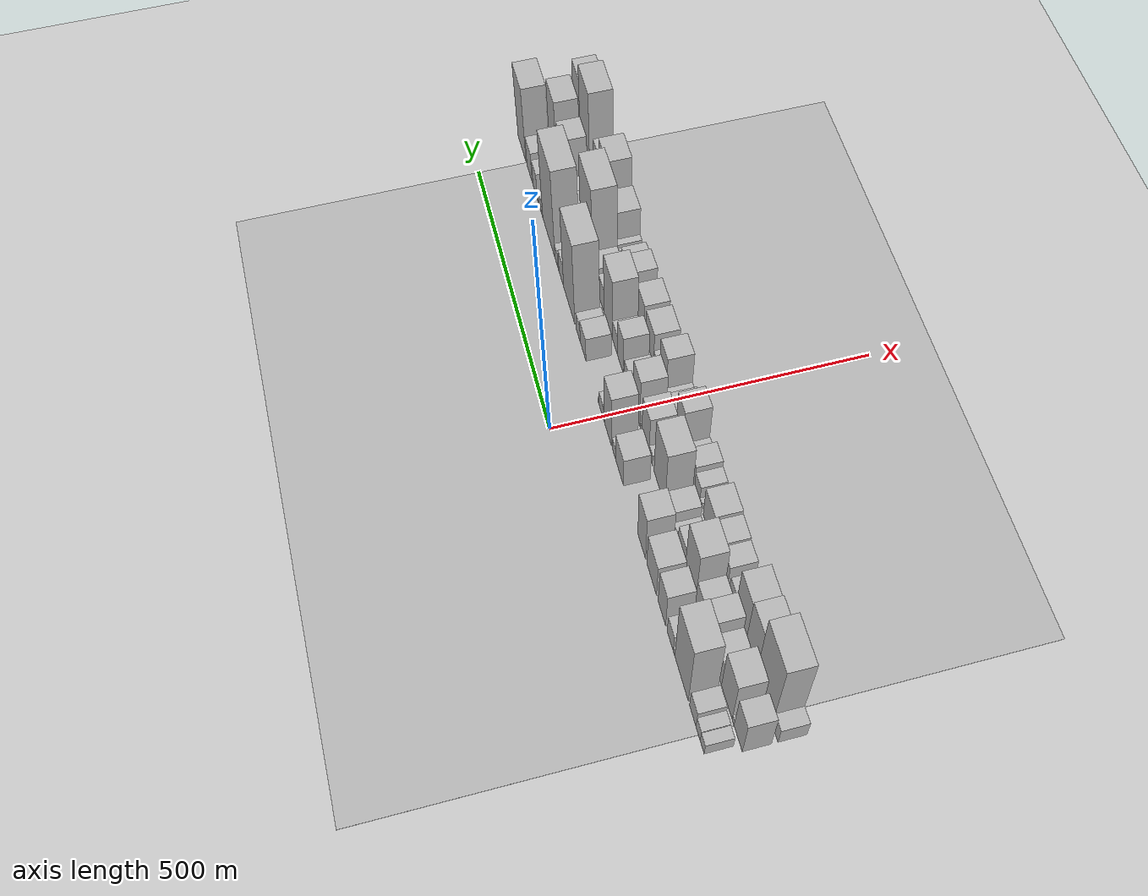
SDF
<?xml version="1.0" encoding="utf-8"?>

<sdf version="1.6">

   <world name="default">

      <gui fullscreen="0">

         <camera name="user_camera">

            <pose>-15 0 4.57585 0 0 0</pose>

            <view_controller>orbit</view_controller>

         </camera>

      </gui>

      <scene>

         <sky>

           <clouds>

             <speed>12</speed>

           </clouds>

         </sky>

         <ambient>0.4 0.4 0.4 1</ambient>

         <background>0.7 0.7 0.7 1</background>

         <shadows>1</shadows>

      </scene>

      <gravity>0 0 -9.8066</gravity>

      <magnetic_field>6e-06 2.3e-05 -4.2e-05</magnetic_field>

      <physics default="0" name="default_physics" type="ode">

         <ode>

            <solver>

               <type>quick</type>

               <iters>10</iters>

               <sor>1.0</sor>

               <use_dynamic_moi_rescaling>0</use_dynamic_moi_rescaling>

            </solver>

            <constraints>

               <cfm>0</cfm>

               <erp>0.2</erp>

               <contact_max_correcting_vel>100</contact_max_correcting_vel>

               <contact_surface_layer>0.001</contact_surface_layer>

            </constraints>

         </ode>

         <max_step_size>0.004</max_step_size>

         <real_time_factor>1</real_time_factor>

         <real_time_update_rate>250</real_time_update_rate>

      </physics>

      <light name="sun" type="directional">

         <cast_shadows>1</cast_shadows>

         <pose>0 0 10 0 0 0</pose>

         <diffuse>0.8 0.8 0.8 1</diffuse>

         <specular>0.2 0.2 0.2 1</specular>

         <attenuation>

            <range>1000</range>

            <constant>0.9</constant>

            <linear>0.01</linear>

            <quadratic>0.001</quadratic>

         </attenuation>

         <direction>-0.5 0.1 -0.9</direction>

      </light>

      <include>

         <name>ground_plane_1</name>

         <uri>model://HANNAS_ground_plane</uri>

         <pose>0 0 0  0 0 0</pose>

      </include>

      <include>

         <name>ground_plane_2</name>

         <uri>model://HANNAS_ground_plane</uri>

         <pose>100 0 0  0 0 0</pose>

      </include>

      <model name="building_1">

         <static>1</static>

         <pose frame="">100.0000 -516.9672 0 0.000000 0.000000 0.000000</pose>

         <link name="link">

            <pose frame="">0 0 16.50 0 0 0</pose>

            <collision name="collision">

               <geometry>

                  <box>

                     <size>40.0000 18.0656 33.0000</size>

                  </box>

               </geometry>

               <max_contacts>10</max_contacts>

               <surface>

                  <contact>

                     <ode/>

                  </contact>

                  <bounce/>

                  <friction>

                     <torsional>

                        <ode/>

                     </torsional>

                     <ode/>

                  </friction>

               </surface>

            </collision>

            <visual name="visual">

               <cast_shadows>0</cast_shadows>

               <geometry>

                  <box>

                     <size>40.0000 18.0656 33.0000</size>

                  </box>

               </geometry>

               <material>

                  <script>

                     <uri>model://HANNAS_wall/materials/scripts</uri>

                     <uri>model://HANNAS_wall/materials/textures</uri>

                     <name>vrc/HANNAS_wall</name>

                  </script>

               </material>

            </visual>

            <self_collide>0</self_collide>

            <enable_wind>0</enable_wind>

            <kinematic>0</kinematic>

         </link>

      </model>

      <model name="building_2">

         <static>1</static>

         <pose frame="">100.0000 -498.0871 0 0.000000 0.000000 0.000000</pose>

         <link name="link">

            <pose frame="">0 0 18.00 0 0 0</pose>

            <collision name="collision">

               <geometry>

                  <box>

                     <size>40.0000 19.6946 36.0000</size>

                  </box>

               </geometry>

               <max_contacts>10</max_contacts>

               <surface>

                  <contact>

                     <ode/>

                  </contact>

                  <bounce/>

                  <friction>

                     <torsional>

                        <ode/>

                     </torsional>

                     <ode/>

                  </friction>

               </surface>

            </collision>

            <visual name="visual">

               <cast_shadows>0</cast_shadows>

               <geometry>

                  <box>

                     <size>40.0000 19.6946 36.0000</size>

                  </box>

               </geometry>

               <material>

                  <script>

                     <uri>model://HANNAS_wall/materials/scripts</uri>

                     <uri>model://HANNAS_wall/materials/textures</uri>

                     <name>vrc/HANNAS_wall</name>

                  </script>

               </material>

            </visual>

            <self_collide>0</self_collide>

            <enable_wind>0</enable_wind>

            <kinematic>0</kinematic>

         </link>

      </model>

      <model name="building_3">

         <static>1</static>

         <pose frame="">100.0000 -473.3525 0 0.000000 0.000000 0.000000</pose>

         <link name="link">

            <pose frame="">0 0 25.50 0 0 0</pose>

            <collision name="collision">

               <geometry>

                  <box>

                     <size>40.0000 29.7748 51.0000</size>

                  </box>

               </geometry>

               <max_contacts>10</max_contacts>

               <surface>

                  <contact>

                     <ode/>

                  </contact>

                  <bounce/>

                  <friction>

                     <torsional>

                        <ode/>

                     </torsional>

                     <ode/>

                  </friction>

               </surface>

            </collision>

            <visual name="visual">

               <cast_shadows>0</cast_shadows>

               <geometry>

                  <box>

                     <size>40.0000 29.7748 51.0000</size>

                  </box>

               </geometry>

               <material>

                  <script>

                     <uri>model://HANNAS_wall/materials/scripts</uri>

                     <uri>model://HANNAS_wall/materials/textures</uri>

                     <name>vrc/HANNAS_wall</name>

                  </script>

               </material>

            </visual>

            <self_collide>0</self_collide>

            <enable_wind>0</enable_wind>

            <kinematic>0</kinematic>

         </link>

      </model>

      <model name="building_4">

         <static>1</static>

         <pose frame="">100.0000 -420.0573 0 0.000000 0.000000 0.000000</pose>

         <link name="link">

            <pose frame="">0 0 88.50 0 0 0</pose>

            <collision name="collision">

               <geometry>

                  <box>

                     <size>40.0000 64.8154 177.0000</size>

                  </box>

               </geometry>

               <max_contacts>10</max_contacts>

               <surface>

                  <contact>

                     <ode/>

                  </contact>

                  <bounce/>

                  <friction>

                     <torsional>

                        <ode/>

                     </torsional>

                     <ode/>

                  </friction>

               </surface>

            </collision>

            <visual name="visual">

               <cast_shadows>0</cast_shadows>

               <geometry>

                  <box>

                     <size>40.0000 64.8154 177.0000</size>

                  </box>

               </geometry>

               <material>

                  <script>

                     <uri>model://HANNAS_wall/materials/scripts</uri>

                     <uri>model://HANNAS_wall/materials/textures</uri>

                     <name>vrc/HANNAS_wall</name>

                  </script>

               </material>

            </visual>

            <self_collide>0</self_collide>

            <enable_wind>0</enable_wind>

            <kinematic>0</kinematic>

         </link>

      </model>

      <model name="building_5">

         <static>1</static>

         <pose frame="">100.0000 -383.9254 0 0.000000 0.000000 0.000000</pose>

         <link name="link">

            <pose frame="">0 0 9.00 0 0 0</pose>

            <collision name="collision">

               <geometry>

                  <box>

                     <size>40.0000 7.4484 18.0000</size>

                  </box>

               </geometry>

               <max_contacts>10</max_contacts>

               <surface>

                  <contact>

                     <ode/>

                  </contact>

                  <bounce/>

                  <friction>

                     <torsional>

                        <ode/>

                     </torsional>

                     <ode/>

                  </friction>

               </surface>

            </collision>

            <visual name="visual">

               <cast_shadows>0</cast_shadows>

               <geometry>

                  <box>

                     <size>40.0000 7.4484 18.0000</size>

                  </box>

               </geometry>

               <material>

                  <script>

                     <uri>model://HANNAS_wall/materials/scripts</uri>

                     <uri>model://HANNAS_wall/materials/textures</uri>

                     <name>vrc/HANNAS_wall</name>

                  </script>

               </material>

            </visual>

            <self_collide>0</self_collide>

            <enable_wind>0</enable_wind>

            <kinematic>0</kinematic>

         </link>

      </model>

      <model name="building_6">

         <static>1</static>

         <pose frame="">100.0000 -365.1987 0 0.000000 0.000000 0.000000</pose>

         <link name="link">

            <pose frame="">0 0 25.50 0 0 0</pose>

            <collision name="collision">

               <geometry>

                  <box>

                     <size>40.0000 30.0050 51.0000</size>

                  </box>

               </geometry>

               <max_contacts>10</max_contacts>

               <surface>

                  <contact>

                     <ode/>

                  </contact>

                  <bounce/>

                  <friction>

                     <torsional>

                        <ode/>

                     </torsional>

                     <ode/>

                  </friction>

               </surface>

            </collision>

            <visual name="visual">

               <cast_shadows>0</cast_shadows>

               <geometry>

                  <box>

                     <size>40.0000 30.0050 51.0000</size>

                  </box>

               </geometry>

               <material>

                  <script>

                     <uri>model://HANNAS_wall/materials/scripts</uri>

                     <uri>model://HANNAS_wall/materials/textures</uri>

                     <name>vrc/HANNAS_wall</name>

                  </script>

               </material>

            </visual>

            <self_collide>0</self_collide>

            <enable_wind>0</enable_wind>

            <kinematic>0</kinematic>

         </link>

      </model>

      <model name="building_7">

         <static>1</static>

         <pose frame="">100.0000 -323.3096 0 0.000000 0.000000 0.000000</pose>

         <link name="link">

            <pose frame="">0 0 48.00 0 0 0</pose>

            <collision name="collision">

               <geometry>

                  <box>

                     <size>40.0000 37.7732 96.0000</size>

                  </box>

               </geometry>

               <max_contacts>10</max_contacts>

               <surface>

                  <contact>

                     <ode/>

                  </contact>

                  <bounce/>

                  <friction>

                     <torsional>

                        <ode/>

                     </torsional>

                     <ode/>

                  </friction>

               </surface>

            </collision>

            <visual name="visual">

               <cast_shadows>0</cast_shadows>

               <geometry>

                  <box>

                     <size>40.0000 37.7732 96.0000</size>

                  </box>

               </geometry>

               <material>

                  <script>

                     <uri>model://HANNAS_wall/materials/scripts</uri>

                     <uri>model://HANNAS_wall/materials/textures</uri>

                     <name>vrc/HANNAS_wall</name>

                  </script>

               </material>

            </visual>

            <self_collide>0</self_collide>

            <enable_wind>0</enable_wind>

            <kinematic>0</kinematic>

         </link>

      </model>

      <model name="building_8">

         <static>1</static>

         <pose frame="">100.0000 -271.5236 0 0.000000 0.000000 0.000000</pose>

         <link name="link">

            <pose frame="">0 0 45.00 0 0 0</pose>

            <collision name="collision">

               <geometry>

                  <box>

                     <size>40.0000 49.7988 90.0000</size>

                  </box>

               </geometry>

               <max_contacts>10</max_contacts>

               <surface>

                  <contact>

                     <ode/>

                  </contact>

                  <bounce/>

                  <friction>

                     <torsional>

                        <ode/>

                     </torsional>

                     <ode/>

                  </friction>

               </surface>

            </collision>

            <visual name="visual">

               <cast_shadows>0</cast_shadows>

               <geometry>

                  <box>

                     <size>40.0000 49.7988 90.0000</size>

                  </box>

               </geometry>

               <material>

                  <script>

                     <uri>model://HANNAS_wall/materials/scripts</uri>

                     <uri>model://HANNAS_wall/materials/textures</uri>

                     <name>vrc/HANNAS_wall</name>

                  </script>

               </material>

            </visual>

            <self_collide>0</self_collide>

            <enable_wind>0</enable_wind>

            <kinematic>0</kinematic>

         </link>

      </model>

      <model name="building_9">

         <static>1</static>

         <pose frame="">100.0000 -219.0494 0 0.000000 0.000000 0.000000</pose>

         <link name="link">

            <pose frame="">0 0 61.50 0 0 0</pose>

            <collision name="collision">

               <geometry>

                  <box>

                     <size>40.0000 41.1495 123.0000</size>

                  </box>

               </geometry>

               <max_contacts>10</max_contacts>

               <surface>

                  <contact>

                     <ode/>

                  </contact>

                  <bounce/>

                  <friction>

                     <torsional>

                        <ode/>

                     </torsional>

                     <ode/>

                  </friction>

               </surface>

            </collision>

            <visual name="visual">

               <cast_shadows>0</cast_shadows>

               <geometry>

                  <box>

                     <size>40.0000 41.1495 123.0000</size>

                  </box>

               </geometry>

               <material>

                  <script>

                     <uri>model://HANNAS_wall/materials/scripts</uri>

                     <uri>model://HANNAS_wall/materials/textures</uri>

                     <name>vrc/HANNAS_wall</name>

                  </script>

               </material>

            </visual>

            <self_collide>0</self_collide>

            <enable_wind>0</enable_wind>

            <kinematic>0</kinematic>

         </link>

      </model>

      <model name="building_10">

         <static>1</static>

         <pose frame="">100.0000 -98.0714 0 0.000000 0.000000 0.000000</pose>

         <link name="link">

            <pose frame="">0 0 37.50 0 0 0</pose>

            <collision name="collision">

               <geometry>

                  <box>

                     <size>40.0000 44.2688 75.0000</size>

                  </box>

               </geometry>

               <max_contacts>10</max_contacts>

               <surface>

                  <contact>

                     <ode/>

                  </contact>

                  <bounce/>

                  <friction>

                     <torsional>

                        <ode/>

                     </torsional>

                     <ode/>

                  </friction>

               </surface>

            </collision>

            <visual name="visual">

               <cast_shadows>0</cast_shadows>

               <geometry>

                  <box>

                     <size>40.0000 44.2688 75.0000</size>

                  </box>

               </geometry>

               <material>

                  <script>

                     <uri>model://HANNAS_wall/materials/scripts</uri>

                     <uri>model://HANNAS_wall/materials/textures</uri>

                     <name>vrc/HANNAS_wall</name>

                  </script>

               </material>

            </visual>

            <self_collide>0</self_collide>

            <enable_wind>0</enable_wind>

            <kinematic>0</kinematic>

         </link>

      </model>

      <model name="building_11">

         <static>1</static>

         <pose frame="">100.0000 -66.1817 0 0.000000 0.000000 0.000000</pose>

         <link name="link">

            <pose frame="">0 0 16.50 0 0 0</pose>

            <collision name="collision">

               <geometry>

                  <box>

                     <size>40.0000 19.5107 33.0000</size>

                  </box>

               </geometry>

               <max_contacts>10</max_contacts>

               <surface>

                  <contact>

                     <ode/>

                  </contact>

                  <bounce/>

                  <friction>

                     <torsional>

                        <ode/>

                     </torsional>

                     <ode/>

                  </friction>

               </surface>

            </collision>

            <visual name="visual">

               <cast_shadows>0</cast_shadows>

               <geometry>

                  <box>

                     <size>40.0000 19.5107 33.0000</size>

                  </box>

               </geometry>

               <material>

                  <script>

                     <uri>model://HANNAS_wall/materials/scripts</uri>

                     <uri>model://HANNAS_wall/materials/textures</uri>

                     <name>vrc/HANNAS_wall</name>

                  </script>

               </material>

            </visual>

            <self_collide>0</self_collide>

            <enable_wind>0</enable_wind>

            <kinematic>0</kinematic>

         </link>

      </model>

      <model name="building_12">

         <static>1</static>

         <pose frame="">100.0000 -32.0604 0 0.000000 0.000000 0.000000</pose>

         <link name="link">

            <pose frame="">0 0 66.00 0 0 0</pose>

            <collision name="collision">

               <geometry>

                  <box>

                     <size>40.0000 40.7318 132.0000</size>

                  </box>

               </geometry>

               <max_contacts>10</max_contacts>

               <surface>

                  <contact>

                     <ode/>

                  </contact>

                  <bounce/>

                  <friction>

                     <torsional>

                        <ode/>

                     </torsional>

                     <ode/>

                  </friction>

               </surface>

            </collision>

            <visual name="visual">

               <cast_shadows>0</cast_shadows>

               <geometry>

                  <box>

                     <size>40.0000 40.7318 132.0000</size>

                  </box>

               </geometry>

               <material>

                  <script>

                     <uri>model://HANNAS_wall/materials/scripts</uri>

                     <uri>model://HANNAS_wall/materials/textures</uri>

                     <name>vrc/HANNAS_wall</name>

                  </script>

               </material>

            </visual>

            <self_collide>0</self_collide>

            <enable_wind>0</enable_wind>

            <kinematic>0</kinematic>

         </link>

      </model>

      <model name="building_13">

         <static>1</static>

         <pose frame="">100.0000 -6.9172 0 0.000000 0.000000 0.000000</pose>

         <link name="link">

            <pose frame="">0 0 10.50 0 0 0</pose>

            <collision name="collision">

               <geometry>

                  <box>

                     <size>40.0000 9.5545 21.0000</size>

                  </box>

               </geometry>

               <max_contacts>10</max_contacts>

               <surface>

                  <contact>

                     <ode/>

                  </contact>

                  <bounce/>

                  <friction>

                     <torsional>

                        <ode/>

                     </torsional>

                     <ode/>

                  </friction>

               </surface>

            </collision>

            <visual name="visual">

               <cast_shadows>0</cast_shadows>

               <geometry>

                  <box>

                     <size>40.0000 9.5545 21.0000</size>

                  </box>

               </geometry>

               <material>

                  <script>

                     <uri>model://HANNAS_wall/materials/scripts</uri>

                     <uri>model://HANNAS_wall/materials/textures</uri>

                     <name>vrc/HANNAS_wall</name>

                  </script>

               </material>

            </visual>

            <self_collide>0</self_collide>

            <enable_wind>0</enable_wind>

            <kinematic>0</kinematic>

         </link>

      </model>

      <model name="building_14">

         <static>1</static>

         <pose frame="">100.0000 8.6215 0 0.000000 0.000000 0.000000</pose>

         <link name="link">

            <pose frame="">0 0 19.50 0 0 0</pose>

            <collision name="collision">

               <geometry>

                  <box>

                     <size>40.0000 21.5228 39.0000</size>

                  </box>

               </geometry>

               <max_contacts>10</max_contacts>

               <surface>

                  <contact>

                     <ode/>

                  </contact>

                  <bounce/>

                  <friction>

                     <torsional>

                        <ode/>

                     </torsional>

                     <ode/>

                  </friction>

               </surface>

            </collision>

            <visual name="visual">

               <cast_shadows>0</cast_shadows>

               <geometry>

                  <box>

                     <size>40.0000 21.5228 39.0000</size>

                  </box>

               </geometry>

               <material>

                  <script>

                     <uri>model://HANNAS_wall/materials/scripts</uri>

                     <uri>model://HANNAS_wall/materials/textures</uri>

                     <name>vrc/HANNAS_wall</name>

                  </script>

               </material>

            </visual>

            <self_collide>0</self_collide>

            <enable_wind>0</enable_wind>

            <kinematic>0</kinematic>

         </link>

      </model>

      <model name="building_15">

         <static>1</static>

         <pose frame="">100.0000 22.6645 0 0.000000 0.000000 0.000000</pose>

         <link name="link">

            <pose frame="">0 0 7.50 0 0 0</pose>

            <collision name="collision">

               <geometry>

                  <box>

                     <size>40.0000 6.5633 15.0000</size>

                  </box>

               </geometry>

               <max_contacts>10</max_contacts>

               <surface>

                  <contact>

                     <ode/>

                  </contact>

                  <bounce/>

                  <friction>

                     <torsional>

                        <ode/>

                     </torsional>

                     <ode/>

                  </friction>

               </surface>

            </collision>

            <visual name="visual">

               <cast_shadows>0</cast_shadows>

               <geometry>

                  <box>

                     <size>40.0000 6.5633 15.0000</size>

                  </box>

               </geometry>

               <material>

                  <script>

                     <uri>model://HANNAS_wall/materials/scripts</uri>

                     <uri>model://HANNAS_wall/materials/textures</uri>

                     <name>vrc/HANNAS_wall</name>

                  </script>

               </material>

            </visual>

            <self_collide>0</self_collide>

            <enable_wind>0</enable_wind>

            <kinematic>0</kinematic>

         </link>

      </model>

      <model name="building_16">

         <static>1</static>

         <pose frame="">100.0000 116.9736 0 0.000000 0.000000 0.000000</pose>

         <link name="link">

            <pose frame="">0 0 30.00 0 0 0</pose>

            <collision name="collision">

               <geometry>

                  <box>

                     <size>40.0000 35.3516 60.0000</size>

                  </box>

               </geometry>

               <max_contacts>10</max_contacts>

               <surface>

                  <contact>

                     <ode/>

                  </contact>

                  <bounce/>

                  <friction>

                     <torsional>

                        <ode/>

                     </torsional>

                     <ode/>

                  </friction>

               </surface>

            </collision>

            <visual name="visual">

               <cast_shadows>0</cast_shadows>

               <geometry>

                  <box>

                     <size>40.0000 35.3516 60.0000</size>

                  </box>

               </geometry>

               <material>

                  <script>

                     <uri>model://HANNAS_wall/materials/scripts</uri>

                     <uri>model://HANNAS_wall/materials/textures</uri>

                     <name>vrc/HANNAS_wall</name>

                  </script>

               </material>

            </visual>

            <self_collide>0</self_collide>

            <enable_wind>0</enable_wind>

            <kinematic>0</kinematic>

         </link>

      </model>

      <model name="building_17">

         <static>1</static>

         <pose frame="">100.0000 147.3279 0 0.000000 0.000000 0.000000</pose>

         <link name="link">

            <pose frame="">0 0 22.50 0 0 0</pose>

            <collision name="collision">

               <geometry>

                  <box>

                     <size>40.0000 25.3570 45.0000</size>

                  </box>

               </geometry>

               <max_contacts>10</max_contacts>

               <surface>

                  <contact>

                     <ode/>

                  </contact>

                  <bounce/>

                  <friction>

                     <torsional>

                        <ode/>

                     </torsional>

                     <ode/>

                  </friction>

               </surface>

            </collision>

            <visual name="visual">

               <cast_shadows>0</cast_shadows>

               <geometry>

                  <box>

                     <size>40.0000 25.3570 45.0000</size>

                  </box>

               </geometry>

               <material>

                  <script>

                     <uri>model://HANNAS_wall/materials/scripts</uri>

                     <uri>model://HANNAS_wall/materials/textures</uri>

                     <name>vrc/HANNAS_wall</name>

                  </script>

               </material>

            </visual>

            <self_collide>0</self_collide>

            <enable_wind>0</enable_wind>

            <kinematic>0</kinematic>

         </link>

      </model>

      <model name="building_18">

         <static>1</static>

         <pose frame="">100.0000 205.0709 0 0.000000 0.000000 0.000000</pose>

         <link name="link">

            <pose frame="">0 0 100.50 0 0 0</pose>

            <collision name="collision">

               <geometry>

                  <box>

                     <size>40.0000 72.1291 201.0000</size>

                  </box>

               </geometry>

               <max_contacts>10</max_contacts>

               <surface>

                  <contact>

                     <ode/>

                  </contact>

                  <bounce/>

                  <friction>

                     <torsional>

                        <ode/>

                     </torsional>

                     <ode/>

                  </friction>

               </surface>

            </collision>

            <visual name="visual">

               <cast_shadows>0</cast_shadows>

               <geometry>

                  <box>

                     <size>40.0000 72.1291 201.0000</size>

                  </box>

               </geometry>

               <material>

                  <script>

                     <uri>model://HANNAS_wall/materials/scripts</uri>

                     <uri>model://HANNAS_wall/materials/textures</uri>

                     <name>vrc/HANNAS_wall</name>

                  </script>

               </material>

            </visual>

            <self_collide>0</self_collide>

            <enable_wind>0</enable_wind>

            <kinematic>0</kinematic>

         </link>

      </model>

      <model name="building_19">

         <static>1</static>

         <pose frame="">100.0000 256.4141 0 0.000000 0.000000 0.000000</pose>

         <link name="link">

            <pose frame="">0 0 28.50 0 0 0</pose>

            <collision name="collision">

               <geometry>

                  <box>

                     <size>40.0000 30.5573 57.0000</size>

                  </box>

               </geometry>

               <max_contacts>10</max_contacts>

               <surface>

                  <contact>

                     <ode/>

                  </contact>

                  <bounce/>

                  <friction>

                     <torsional>

                        <ode/>

                     </torsional>

                     <ode/>

                  </friction>

               </surface>

            </collision>

            <visual name="visual">

               <cast_shadows>0</cast_shadows>

               <geometry>

                  <box>

                     <size>40.0000 30.5573 57.0000</size>

                  </box>

               </geometry>

               <material>

                  <script>

                     <uri>model://HANNAS_wall/materials/scripts</uri>

                     <uri>model://HANNAS_wall/materials/textures</uri>

                     <name>vrc/HANNAS_wall</name>

                  </script>

               </material>

            </visual>

            <self_collide>0</self_collide>

            <enable_wind>0</enable_wind>

            <kinematic>0</kinematic>

         </link>

      </model>

      <model name="building_20">

         <static>1</static>

         <pose frame="">100.0000 274.9264 0 0.000000 0.000000 0.000000</pose>

         <link name="link">

            <pose frame="">0 0 7.50 0 0 0</pose>

            <collision name="collision">

               <geometry>

                  <box>

                     <size>40.0000 6.4674 15.0000</size>

                  </box>

               </geometry>

               <max_contacts>10</max_contacts>

               <surface>

                  <contact>

                     <ode/>

                  </contact>

                  <bounce/>

                  <friction>

                     <torsional>

                        <ode/>

                     </torsional>

                     <ode/>

                  </friction>

               </surface>

            </collision>

            <visual name="visual">

               <cast_shadows>0</cast_shadows>

               <geometry>

                  <box>

                     <size>40.0000 6.4674 15.0000</size>

                  </box>

               </geometry>

               <material>

                  <script>

                     <uri>model://HANNAS_wall/materials/scripts</uri>

                     <uri>model://HANNAS_wall/materials/textures</uri>

                     <name>vrc/HANNAS_wall</name>

                  </script>

               </material>

            </visual>

            <self_collide>0</self_collide>

            <enable_wind>0</enable_wind>

            <kinematic>0</kinematic>

         </link>

      </model>

      <model name="building_21">

         <static>1</static>

         <pose frame="">100.0000 288.3345 0 0.000000 0.000000 0.000000</pose>

         <link name="link">

            <pose frame="">0 0 19.50 0 0 0</pose>

            <collision name="collision">

               <geometry>

                  <box>

                     <size>40.0000 20.3488 39.0000</size>

                  </box>

               </geometry>

               <max_contacts>10</max_contacts>

               <surface>

                  <contact>

                     <ode/>

                  </contact>

                  <bounce/>

                  <friction>

                     <torsional>

                        <ode/>

                     </torsional>

                     <ode/>

                  </friction>

               </surface>

            </collision>

            <visual name="visual">

               <cast_shadows>0</cast_shadows>

               <geometry>

                  <box>

                     <size>40.0000 20.3488 39.0000</size>

                  </box>

               </geometry>

               <material>

                  <script>

                     <uri>model://HANNAS_wall/materials/scripts</uri>

                     <uri>model://HANNAS_wall/materials/textures</uri>

                     <name>vrc/HANNAS_wall</name>

                  </script>

               </material>

            </visual>

            <self_collide>0</self_collide>

            <enable_wind>0</enable_wind>

            <kinematic>0</kinematic>

         </link>

      </model>

      <model name="building_22">

         <static>1</static>

         <pose frame="">100.0000 340.1343 0 0.000000 0.000000 0.000000</pose>

         <link name="link">

            <pose frame="">0 0 106.50 0 0 0</pose>

            <collision name="collision">

               <geometry>

                  <box>

                     <size>40.0000 83.2506 213.0000</size>

                  </box>

               </geometry>

               <max_contacts>10</max_contacts>

               <surface>

                  <contact>

                     <ode/>

                  </contact>

                  <bounce/>

                  <friction>

                     <torsional>

                        <ode/>

                     </torsional>

                     <ode/>

                  </friction>

               </surface>

            </collision>

            <visual name="visual">

               <cast_shadows>0</cast_shadows>

               <geometry>

                  <box>

                     <size>40.0000 83.2506 213.0000</size>

                  </box>

               </geometry>

               <material>

                  <script>

                     <uri>model://HANNAS_wall/materials/scripts</uri>

                     <uri>model://HANNAS_wall/materials/textures</uri>

                     <name>vrc/HANNAS_wall</name>

                  </script>

               </material>

            </visual>

            <self_collide>0</self_collide>

            <enable_wind>0</enable_wind>

            <kinematic>0</kinematic>

         </link>

      </model>

      <model name="building_23">

         <static>1</static>

         <pose frame="">100.0000 387.8047 0 0.000000 0.000000 0.000000</pose>

         <link name="link">

            <pose frame="">0 0 13.50 0 0 0</pose>

            <collision name="collision">

               <geometry>

                  <box>

                     <size>40.0000 12.0903 27.0000</size>

                  </box>

               </geometry>

               <max_contacts>10</max_contacts>

               <surface>

                  <contact>

                     <ode/>

                  </contact>

                  <bounce/>

                  <friction>

                     <torsional>

                        <ode/>

                     </torsional>

                     <ode/>

                  </friction>

               </surface>

            </collision>

            <visual name="visual">

               <cast_shadows>0</cast_shadows>

               <geometry>

                  <box>

                     <size>40.0000 12.0903 27.0000</size>

                  </box>

               </geometry>

               <material>

                  <script>

                     <uri>model://HANNAS_wall/materials/scripts</uri>

                     <uri>model://HANNAS_wall/materials/textures</uri>

                     <name>vrc/HANNAS_wall</name>

                  </script>

               </material>

            </visual>

            <self_collide>0</self_collide>

            <enable_wind>0</enable_wind>

            <kinematic>0</kinematic>

         </link>

      </model>

      <model name="building_24">

         <static>1</static>

         <pose frame="">100.0000 402.1680 0 0.000000 0.000000 0.000000</pose>

         <link name="link">

            <pose frame="">0 0 16.50 0 0 0</pose>

            <collision name="collision">

               <geometry>

                  <box>

                     <size>40.0000 16.6363 33.0000</size>

                  </box>

               </geometry>

               <max_contacts>10</max_contacts>

               <surface>

                  <contact>

                     <ode/>

                  </contact>

                  <bounce/>

                  <friction>

                     <torsional>

                        <ode/>

                     </torsional>

                     <ode/>

                  </friction>

               </surface>

            </collision>

            <visual name="visual">

               <cast_shadows>0</cast_shadows>

               <geometry>

                  <box>

                     <size>40.0000 16.6363 33.0000</size>

                  </box>

               </geometry>

               <material>

                  <script>

                     <uri>model://HANNAS_wall/materials/scripts</uri>

                     <uri>model://HANNAS_wall/materials/textures</uri>

                     <name>vrc/HANNAS_wall</name>

                  </script>

               </material>

            </visual>

            <self_collide>0</self_collide>

            <enable_wind>0</enable_wind>

            <kinematic>0</kinematic>

         </link>

      </model>

      <model name="building_25">

         <static>1</static>

         <pose frame="">100.0000 415.1284 0 0.000000 0.000000 0.000000</pose>

         <link name="link">

            <pose frame="">0 0 10.50 0 0 0</pose>

            <collision name="collision">

               <geometry>

                  <box>

                     <size>40.0000 9.2845 21.0000</size>

                  </box>

               </geometry>

               <max_contacts>10</max_contacts>

               <surface>

                  <contact>

                     <ode/>

                  </contact>

                  <bounce/>

                  <friction>

                     <torsional>

                        <ode/>

                     </torsional>

                     <ode/>

                  </friction>

               </surface>

            </collision>

            <visual name="visual">

               <cast_shadows>0</cast_shadows>

               <geometry>

                  <box>

                     <size>40.0000 9.2845 21.0000</size>

                  </box>

               </geometry>

               <material>

                  <script>

                     <uri>model://HANNAS_wall/materials/scripts</uri>

                     <uri>model://HANNAS_wall/materials/textures</uri>

                     <name>vrc/HANNAS_wall</name>

                  </script>

               </material>

            </visual>

            <self_collide>0</self_collide>

            <enable_wind>0</enable_wind>

            <kinematic>0</kinematic>

         </link>

      </model>

      <model name="building_26">

         <static>1</static>

         <pose frame="">100.0000 435.5712 0 0.000000 0.000000 0.000000</pose>

         <link name="link">

            <pose frame="">0 0 31.50 0 0 0</pose>

            <collision name="collision">

               <geometry>

                  <box>

                     <size>40.0000 31.6012 63.0000</size>

                  </box>

               </geometry>

               <max_contacts>10</max_contacts>

               <surface>

                  <contact>

                     <ode/>

                  </contact>

                  <bounce/>

                  <friction>

                     <torsional>

                        <ode/>

                     </torsional>

                     <ode/>

                  </friction>

               </surface>

            </collision>

            <visual name="visual">

               <cast_shadows>0</cast_shadows>

               <geometry>

                  <box>

                     <size>40.0000 31.6012 63.0000</size>

                  </box>

               </geometry>

               <material>

                  <script>

                     <uri>model://HANNAS_wall/materials/scripts</uri>

                     <uri>model://HANNAS_wall/materials/textures</uri>

                     <name>vrc/HANNAS_wall</name>

                  </script>

               </material>

            </visual>

            <self_collide>0</self_collide>

            <enable_wind>0</enable_wind>

            <kinematic>0</kinematic>

         </link>

      </model>

      <model name="building_27">

         <static>1</static>

         <pose frame="">100.0000 475.1789 0 0.000000 0.000000 0.000000</pose>

         <link name="link">

            <pose frame="">0 0 36.00 0 0 0</pose>

            <collision name="collision">

               <geometry>

                  <box>

                     <size>40.0000 37.6142 72.0000</size>

                  </box>

               </geometry>

               <max_contacts>10</max_contacts>

               <surface>

                  <contact>

                     <ode/>

                  </contact>

                  <bounce/>

                  <friction>

                     <torsional>

                        <ode/>

                     </torsional>

                     <ode/>

                  </friction>

               </surface>

            </collision>

            <visual name="visual">

               <cast_shadows>0</cast_shadows>

               <geometry>

                  <box>

                     <size>40.0000 37.6142 72.0000</size>

                  </box>

               </geometry>

               <material>

                  <script>

                     <uri>model://HANNAS_wall/materials/scripts</uri>

                     <uri>model://HANNAS_wall/materials/textures</uri>

                     <name>vrc/HANNAS_wall</name>

                  </script>

               </material>

            </visual>

            <self_collide>0</self_collide>

            <enable_wind>0</enable_wind>

            <kinematic>0</kinematic>

         </link>

      </model>

      <model name="building_28">

         <static>1</static>

         <pose frame="">100.0000 530.3695 0 0.000000 0.000000 0.000000</pose>

         <link name="link">

            <pose frame="">0 0 87.00 0 0 0</pose>

            <collision name="collision">

               <geometry>

                  <box>

                     <size>40.0000 58.7670 174.0000</size>

                  </box>

               </geometry>

               <max_contacts>10</max_contacts>

               <surface>

                  <contact>

                     <ode/>

                  </contact>

                  <bounce/>

                  <friction>

                     <torsional>

                        <ode/>

                     </torsional>

                     <ode/>

                  </friction>

               </surface>

            </collision>

            <visual name="visual">

               <cast_shadows>0</cast_shadows>

               <geometry>

                  <box>

                     <size>40.0000 58.7670 174.0000</size>

                  </box>

               </geometry>

               <material>

                  <script>

                     <uri>model://HANNAS_wall/materials/scripts</uri>

                     <uri>model://HANNAS_wall/materials/textures</uri>

                     <name>vrc/HANNAS_wall</name>

                  </script>

               </material>

            </visual>

            <self_collide>0</self_collide>

            <enable_wind>0</enable_wind>

            <kinematic>0</kinematic>

         </link>

      </model>

      <model name="building_29">

         <static>1</static>

         <pose frame="">149.0000 -517.9019 0 0.000000 0.000000 0.000000</pose>

         <link name="link">

            <pose frame="">0 0 49.50 0 0 0</pose>

            <collision name="collision">

               <geometry>

                  <box>

                     <size>40.0000 36.1962 99.0000</size>

                  </box>

               </geometry>

               <max_contacts>10</max_contacts>

               <surface>

                  <contact>

                     <ode/>

                  </contact>

                  <bounce/>

                  <friction>

                     <torsional>

                        <ode/>

                     </torsional>

                     <ode/>

                  </friction>

               </surface>

            </collision>

            <visual name="visual">

               <cast_shadows>0</cast_shadows>

               <geometry>

                  <box>

                     <size>40.0000 36.1962 99.0000</size>

                  </box>

               </geometry>

               <material>

                  <script>

                     <uri>model://HANNAS_wall/materials/scripts</uri>

                     <uri>model://HANNAS_wall/materials/textures</uri>

                     <name>vrc/HANNAS_wall</name>

                  </script>

               </material>

            </visual>

            <self_collide>0</self_collide>

            <enable_wind>0</enable_wind>

            <kinematic>0</kinematic>

         </link>

      </model>

      <model name="building_30">

         <static>1</static>

         <pose frame="">149.0000 -495.4424 0 0.000000 0.000000 0.000000</pose>

         <link name="link">

            <pose frame="">0 0 9.00 0 0 0</pose>

            <collision name="collision">

               <geometry>

                  <box>

                     <size>40.0000 8.7228 18.0000</size>

                  </box>

               </geometry>

               <max_contacts>10</max_contacts>

               <surface>

                  <contact>

                     <ode/>

                  </contact>

                  <bounce/>

                  <friction>

                     <torsional>

                        <ode/>

                     </torsional>

                     <ode/>

                  </friction>

               </surface>

            </collision>

            <visual name="visual">

               <cast_shadows>0</cast_shadows>

               <geometry>

                  <box>

                     <size>40.0000 8.7228 18.0000</size>

                  </box>

               </geometry>

               <material>

                  <script>

                     <uri>model://HANNAS_wall/materials/scripts</uri>

                     <uri>model://HANNAS_wall/materials/textures</uri>

                     <name>vrc/HANNAS_wall</name>

                  </script>

               </material>

            </visual>

            <self_collide>0</self_collide>

            <enable_wind>0</enable_wind>

            <kinematic>0</kinematic>

         </link>

      </model>

      <model name="building_31">

         <static>1</static>

         <pose frame="">149.0000 -467.1126 0 0.000000 0.000000 0.000000</pose>

         <link name="link">

            <pose frame="">0 0 60.00 0 0 0</pose>

            <collision name="collision">

               <geometry>

                  <box>

                     <size>40.0000 47.9369 120.0000</size>

                  </box>

               </geometry>

               <max_contacts>10</max_contacts>

               <surface>

                  <contact>

                     <ode/>

                  </contact>

                  <bounce/>

                  <friction>

                     <torsional>

                        <ode/>

                     </torsional>

                     <ode/>

                  </friction>

               </surface>

            </collision>

            <visual name="visual">

               <cast_shadows>0</cast_shadows>

               <geometry>

                  <box>

                     <size>40.0000 47.9369 120.0000</size>

                  </box>

               </geometry>

               <material>

                  <script>

                     <uri>model://HANNAS_wall/materials/scripts</uri>

                     <uri>model://HANNAS_wall/materials/textures</uri>

                     <name>vrc/HANNAS_wall</name>

                  </script>

               </material>

            </visual>

            <self_collide>0</self_collide>

            <enable_wind>0</enable_wind>

            <kinematic>0</kinematic>

         </link>

      </model>

      <model name="building_32">

         <static>1</static>

         <pose frame="">149.0000 -420.7778 0 0.000000 0.000000 0.000000</pose>

         <link name="link">

            <pose frame="">0 0 37.50 0 0 0</pose>

            <collision name="collision">

               <geometry>

                  <box>

                     <size>40.0000 44.7326 75.0000</size>

                  </box>

               </geometry>

               <max_contacts>10</max_contacts>

               <surface>

                  <contact>

                     <ode/>

                  </contact>

                  <bounce/>

                  <friction>

                     <torsional>

                        <ode/>

                     </torsional>

                     <ode/>

                  </friction>

               </surface>

            </collision>

            <visual name="visual">

               <cast_shadows>0</cast_shadows>

               <geometry>

                  <box>

                     <size>40.0000 44.7326 75.0000</size>

                  </box>

               </geometry>

               <material>

                  <script>

                     <uri>model://HANNAS_wall/materials/scripts</uri>

                     <uri>model://HANNAS_wall/materials/textures</uri>

                     <name>vrc/HANNAS_wall</name>

                  </script>

               </material>

            </visual>

            <self_collide>0</self_collide>

            <enable_wind>0</enable_wind>

            <kinematic>0</kinematic>

         </link>

      </model>

      <model name="building_33">

         <static>1</static>

         <pose frame="">149.0000 -380.7269 0 0.000000 0.000000 0.000000</pose>

         <link name="link">

            <pose frame="">0 0 55.50 0 0 0</pose>

            <collision name="collision">

               <geometry>

                  <box>

                     <size>40.0000 35.3693 111.0000</size>

                  </box>

               </geometry>

               <max_contacts>10</max_contacts>

               <surface>

                  <contact>

                     <ode/>

                  </contact>

                  <bounce/>

                  <friction>

                     <torsional>

                        <ode/>

                     </torsional>

                     <ode/>

                  </friction>

               </surface>

            </collision>

            <visual name="visual">

               <cast_shadows>0</cast_shadows>

               <geometry>

                  <box>

                     <size>40.0000 35.3693 111.0000</size>

                  </box>

               </geometry>

               <material>

                  <script>

                     <uri>model://HANNAS_wall/materials/scripts</uri>

                     <uri>model://HANNAS_wall/materials/textures</uri>

                     <name>vrc/HANNAS_wall</name>

                  </script>

               </material>

            </visual>

            <self_collide>0</self_collide>

            <enable_wind>0</enable_wind>

            <kinematic>0</kinematic>

         </link>

      </model>

      <model name="building_34">

         <static>1</static>

         <pose frame="">149.0000 -341.5918 0 0.000000 0.000000 0.000000</pose>

         <link name="link">

            <pose frame="">0 0 36.00 0 0 0</pose>

            <collision name="collision">

               <geometry>

                  <box>

                     <size>40.0000 42.9008 72.0000</size>

                  </box>

               </geometry>

               <max_contacts>10</max_contacts>

               <surface>

                  <contact>

                     <ode/>

                  </contact>

                  <bounce/>

                  <friction>

                     <torsional>

                        <ode/>

                     </torsional>

                     <ode/>

                  </friction>

               </surface>

            </collision>

            <visual name="visual">

               <cast_shadows>0</cast_shadows>

               <geometry>

                  <box>

                     <size>40.0000 42.9008 72.0000</size>

                  </box>

               </geometry>

               <material>

                  <script>

                     <uri>model://HANNAS_wall/materials/scripts</uri>

                     <uri>model://HANNAS_wall/materials/textures</uri>

                     <name>vrc/HANNAS_wall</name>

                  </script>

               </material>

            </visual>

            <self_collide>0</self_collide>

            <enable_wind>0</enable_wind>

            <kinematic>0</kinematic>

         </link>

      </model>

      <model name="building_35">

         <static>1</static>

         <pose frame="">149.0000 -294.4641 0 0.000000 0.000000 0.000000</pose>

         <link name="link">

            <pose frame="">0 0 73.50 0 0 0</pose>

            <collision name="collision">

               <geometry>

                  <box>

                     <size>40.0000 51.3547 147.0000</size>

                  </box>

               </geometry>

               <max_contacts>10</max_contacts>

               <surface>

                  <contact>

                     <ode/>

                  </contact>

                  <bounce/>

                  <friction>

                     <torsional>

                        <ode/>

                     </torsional>

                     <ode/>

                  </friction>

               </surface>

            </collision>

            <visual name="visual">

               <cast_shadows>0</cast_shadows>

               <geometry>

                  <box>

                     <size>40.0000 51.3547 147.0000</size>

                  </box>

               </geometry>

               <material>

                  <script>

                     <uri>model://HANNAS_wall/materials/scripts</uri>

                     <uri>model://HANNAS_wall/materials/textures</uri>

                     <name>vrc/HANNAS_wall</name>

                  </script>

               </material>

            </visual>

            <self_collide>0</self_collide>

            <enable_wind>0</enable_wind>

            <kinematic>0</kinematic>

         </link>

      </model>

      <model name="building_36">

         <static>1</static>

         <pose frame="">149.0000 -250.0624 0 0.000000 0.000000 0.000000</pose>

         <link name="link">

            <pose frame="">0 0 31.50 0 0 0</pose>

            <collision name="collision">

               <geometry>

                  <box>

                     <size>40.0000 37.4487 63.0000</size>

                  </box>

               </geometry>

               <max_contacts>10</max_contacts>

               <surface>

                  <contact>

                     <ode/>

                  </contact>

                  <bounce/>

                  <friction>

                     <torsional>

                        <ode/>

                     </torsional>

                     <ode/>

                  </friction>

               </surface>

            </collision>

            <visual name="visual">

               <cast_shadows>0</cast_shadows>

               <geometry>

                  <box>

                     <size>40.0000 37.4487 63.0000</size>

                  </box>

               </geometry>

               <material>

                  <script>

                     <uri>model://HANNAS_wall/materials/scripts</uri>

                     <uri>model://HANNAS_wall/materials/textures</uri>

                     <name>vrc/HANNAS_wall</name>

                  </script>

               </material>

            </visual>

            <self_collide>0</self_collide>

            <enable_wind>0</enable_wind>

            <kinematic>0</kinematic>

         </link>

      </model>

      <model name="building_37">

         <static>1</static>

         <pose frame="">149.0000 -217.0985 0 0.000000 0.000000 0.000000</pose>

         <link name="link">

            <pose frame="">0 0 15.00 0 0 0</pose>

            <collision name="collision">

               <geometry>

                  <box>

                     <size>40.0000 16.4791 30.0000</size>

                  </box>

               </geometry>

               <max_contacts>10</max_contacts>

               <surface>

                  <contact>

                     <ode/>

                  </contact>

                  <bounce/>

                  <friction>

                     <torsional>

                        <ode/>

                     </torsional>

                     <ode/>

                  </friction>

               </surface>

            </collision>

            <visual name="visual">

               <cast_shadows>0</cast_shadows>

               <geometry>

                  <box>

                     <size>40.0000 16.4791 30.0000</size>

                  </box>

               </geometry>

               <material>

                  <script>

                     <uri>model://HANNAS_wall/materials/scripts</uri>

                     <uri>model://HANNAS_wall/materials/textures</uri>

                     <name>vrc/HANNAS_wall</name>

                  </script>

               </material>

            </visual>

            <self_collide>0</self_collide>

            <enable_wind>0</enable_wind>

            <kinematic>0</kinematic>

         </link>

      </model>

      <model name="building_38">

         <static>1</static>

         <pose frame="">149.0000 -191.1011 0 0.000000 0.000000 0.000000</pose>

         <link name="link">

            <pose frame="">0 0 30.00 0 0 0</pose>

            <collision name="collision">

               <geometry>

                  <box>

                     <size>40.0000 35.5157 60.0000</size>

                  </box>

               </geometry>

               <max_contacts>10</max_contacts>

               <surface>

                  <contact>

                     <ode/>

                  </contact>

                  <bounce/>

                  <friction>

                     <torsional>

                        <ode/>

                     </torsional>

                     <ode/>

                  </friction>

               </surface>

            </collision>

            <visual name="visual">

               <cast_shadows>0</cast_shadows>

               <geometry>

                  <box>

                     <size>40.0000 35.5157 60.0000</size>

                  </box>

               </geometry>

               <material>

                  <script>

                     <uri>model://HANNAS_wall/materials/scripts</uri>

                     <uri>model://HANNAS_wall/materials/textures</uri>

                     <name>vrc/HANNAS_wall</name>

                  </script>

               </material>

            </visual>

            <self_collide>0</self_collide>

            <enable_wind>0</enable_wind>

            <kinematic>0</kinematic>

         </link>

      </model>

      <model name="building_39">

         <static>1</static>

         <pose frame="">149.0000 -137.4377 0 0.000000 0.000000 0.000000</pose>

         <link name="link">

            <pose frame="">0 0 73.50 0 0 0</pose>

            <collision name="collision">

               <geometry>

                  <box>

                     <size>40.0000 57.8110 147.0000</size>

                  </box>

               </geometry>

               <max_contacts>10</max_contacts>

               <surface>

                  <contact>

                     <ode/>

                  </contact>

                  <bounce/>

                  <friction>

                     <torsional>

                        <ode/>

                     </torsional>

                     <ode/>

                  </friction>

               </surface>

            </collision>

            <visual name="visual">

               <cast_shadows>0</cast_shadows>

               <geometry>

                  <box>

                     <size>40.0000 57.8110 147.0000</size>

                  </box>

               </geometry>

               <material>

                  <script>

                     <uri>model://HANNAS_wall/materials/scripts</uri>

                     <uri>model://HANNAS_wall/materials/textures</uri>

                     <name>vrc/HANNAS_wall</name>

                  </script>

               </material>

            </visual>

            <self_collide>0</self_collide>

            <enable_wind>0</enable_wind>

            <kinematic>0</kinematic>

         </link>

      </model>

      <model name="building_40">

         <static>1</static>

         <pose frame="">149.0000 -90.5418 0 0.000000 0.000000 0.000000</pose>

         <link name="link">

            <pose frame="">0 0 15.00 0 0 0</pose>

            <collision name="collision">

               <geometry>

                  <box>

                     <size>40.0000 17.9808 30.0000</size>

                  </box>

               </geometry>

               <max_contacts>10</max_contacts>

               <surface>

                  <contact>

                     <ode/>

                  </contact>

                  <bounce/>

                  <friction>

                     <torsional>

                        <ode/>

                     </torsional>

                     <ode/>

                  </friction>

               </surface>

            </collision>

            <visual name="visual">

               <cast_shadows>0</cast_shadows>

               <geometry>

                  <box>

                     <size>40.0000 17.9808 30.0000</size>

                  </box>

               </geometry>

               <material>

                  <script>

                     <uri>model://HANNAS_wall/materials/scripts</uri>

                     <uri>model://HANNAS_wall/materials/textures</uri>

                     <name>vrc/HANNAS_wall</name>

                  </script>

               </material>

            </visual>

            <self_collide>0</self_collide>

            <enable_wind>0</enable_wind>

            <kinematic>0</kinematic>

         </link>

      </model>

      <model name="building_41">

         <static>1</static>

         <pose frame="">149.0000 -61.8562 0 0.000000 0.000000 0.000000</pose>

         <link name="link">

            <pose frame="">0 0 51.00 0 0 0</pose>

            <collision name="collision">

               <geometry>

                  <box>

                     <size>40.0000 39.3904 102.0000</size>

                  </box>

               </geometry>

               <max_contacts>10</max_contacts>

               <surface>

                  <contact>

                     <ode/>

                  </contact>

                  <bounce/>

                  <friction>

                     <torsional>

                        <ode/>

                     </torsional>

                     <ode/>

                  </friction>

               </surface>

            </collision>

            <visual name="visual">

               <cast_shadows>0</cast_shadows>

               <geometry>

                  <box>

                     <size>40.0000 39.3904 102.0000</size>

                  </box>

               </geometry>

               <material>

                  <script>

                     <uri>model://HANNAS_wall/materials/scripts</uri>

                     <uri>model://HANNAS_wall/materials/textures</uri>

                     <name>vrc/HANNAS_wall</name>

                  </script>

               </material>

            </visual>

            <self_collide>0</self_collide>

            <enable_wind>0</enable_wind>

            <kinematic>0</kinematic>

         </link>

      </model>

      <model name="building_42">

         <static>1</static>

         <pose frame="">149.0000 -37.9044 0 0.000000 0.000000 0.000000</pose>

         <link name="link">

            <pose frame="">0 0 9.00 0 0 0</pose>

            <collision name="collision">

               <geometry>

                  <box>

                     <size>40.0000 8.5134 18.0000</size>

                  </box>

               </geometry>

               <max_contacts>10</max_contacts>

               <surface>

                  <contact>

                     <ode/>

                  </contact>

                  <bounce/>

                  <friction>

                     <torsional>

                        <ode/>

                     </torsional>

                     <ode/>

                  </friction>

               </surface>

            </collision>

            <visual name="visual">

               <cast_shadows>0</cast_shadows>

               <geometry>

                  <box>

                     <size>40.0000 8.5134 18.0000</size>

                  </box>

               </geometry>

               <material>

                  <script>

                     <uri>model://HANNAS_wall/materials/scripts</uri>

                     <uri>model://HANNAS_wall/materials/textures</uri>

                     <name>vrc/HANNAS_wall</name>

                  </script>

               </material>

            </visual>

            <self_collide>0</self_collide>

            <enable_wind>0</enable_wind>

            <kinematic>0</kinematic>

         </link>

      </model>

      <model name="building_43">

         <static>1</static>

         <pose frame="">149.0000 -11.5895 0 0.000000 0.000000 0.000000</pose>

         <link name="link">

            <pose frame="">0 0 61.50 0 0 0</pose>

            <collision name="collision">

               <geometry>

                  <box>

                     <size>40.0000 38.1163 123.0000</size>

                  </box>

               </geometry>

               <max_contacts>10</max_contacts>

               <surface>

                  <contact>

                     <ode/>

                  </contact>

                  <bounce/>

                  <friction>

                     <torsional>

                        <ode/>

                     </torsional>

                     <ode/>

                  </friction>

               </surface>

            </collision>

            <visual name="visual">

               <cast_shadows>0</cast_shadows>

               <geometry>

                  <box>

                     <size>40.0000 38.1163 123.0000</size>

                  </box>

               </geometry>

               <material>

                  <script>

                     <uri>model://HANNAS_wall/materials/scripts</uri>

                     <uri>model://HANNAS_wall/materials/textures</uri>

                     <name>vrc/HANNAS_wall</name>

                  </script>

               </material>

            </visual>

            <self_collide>0</self_collide>

            <enable_wind>0</enable_wind>

            <kinematic>0</kinematic>

         </link>

      </model>

      <model name="building_44">

         <static>1</static>

         <pose frame="">149.0000 15.0906 0 0.000000 0.000000 0.000000</pose>

         <link name="link">

            <pose frame="">0 0 15.00 0 0 0</pose>

            <collision name="collision">

               <geometry>

                  <box>

                     <size>40.0000 15.2440 30.0000</size>

                  </box>

               </geometry>

               <max_contacts>10</max_contacts>

               <surface>

                  <contact>

                     <ode/>

                  </contact>

                  <bounce/>

                  <friction>

                     <torsional>

                        <ode/>

                     </torsional>

                     <ode/>

                  </friction>

               </surface>

            </collision>

            <visual name="visual">

               <cast_shadows>0</cast_shadows>

               <geometry>

                  <box>

                     <size>40.0000 15.2440 30.0000</size>

                  </box>

               </geometry>

               <material>

                  <script>

                     <uri>model://HANNAS_wall/materials/scripts</uri>

                     <uri>model://HANNAS_wall/materials/textures</uri>

                     <name>vrc/HANNAS_wall</name>

                  </script>

               </material>

            </visual>

            <self_collide>0</self_collide>

            <enable_wind>0</enable_wind>

            <kinematic>0</kinematic>

         </link>

      </model>

      <model name="building_45">

         <static>1</static>

         <pose frame="">149.0000 44.5261 0 0.000000 0.000000 0.000000</pose>

         <link name="link">

            <pose frame="">0 0 24.00 0 0 0</pose>

            <collision name="collision">

               <geometry>

                  <box>

                     <size>40.0000 25.6268 48.0000</size>

                  </box>

               </geometry>

               <max_contacts>10</max_contacts>

               <surface>

                  <contact>

                     <ode/>

                  </contact>

                  <bounce/>

                  <friction>

                     <torsional>

                        <ode/>

                     </torsional>

                     <ode/>

                  </friction>

               </surface>

            </collision>

            <visual name="visual">

               <cast_shadows>0</cast_shadows>

               <geometry>

                  <box>

                     <size>40.0000 25.6268 48.0000</size>

                  </box>

               </geometry>

               <material>

                  <script>

                     <uri>model://HANNAS_wall/materials/scripts</uri>

                     <uri>model://HANNAS_wall/materials/textures</uri>

                     <name>vrc/HANNAS_wall</name>

                  </script>

               </material>

            </visual>

            <self_collide>0</self_collide>

            <enable_wind>0</enable_wind>

            <kinematic>0</kinematic>

         </link>

      </model>

      <model name="building_46">

         <static>1</static>

         <pose frame="">149.0000 61.0652 0 0.000000 0.000000 0.000000</pose>

         <link name="link">

            <pose frame="">0 0 9.00 0 0 0</pose>

            <collision name="collision">

               <geometry>

                  <box>

                     <size>40.0000 7.4515 18.0000</size>

                  </box>

               </geometry>

               <max_contacts>10</max_contacts>

               <surface>

                  <contact>

                     <ode/>

                  </contact>

                  <bounce/>

                  <friction>

                     <torsional>

                        <ode/>

                     </torsional>

                     <ode/>

                  </friction>

               </surface>

            </collision>

            <visual name="visual">

               <cast_shadows>0</cast_shadows>

               <geometry>

                  <box>

                     <size>40.0000 7.4515 18.0000</size>

                  </box>

               </geometry>

               <material>

                  <script>

                     <uri>model://HANNAS_wall/materials/scripts</uri>

                     <uri>model://HANNAS_wall/materials/textures</uri>

                     <name>vrc/HANNAS_wall</name>

                  </script>

               </material>

            </visual>

            <self_collide>0</self_collide>

            <enable_wind>0</enable_wind>

            <kinematic>0</kinematic>

         </link>

      </model>

      <model name="building_47">

         <static>1</static>

         <pose frame="">149.0000 81.3213 0 0.000000 0.000000 0.000000</pose>

         <link name="link">

            <pose frame="">0 0 46.50 0 0 0</pose>

            <collision name="collision">

               <geometry>

                  <box>

                     <size>40.0000 33.0606 93.0000</size>

                  </box>

               </geometry>

               <max_contacts>10</max_contacts>

               <surface>

                  <contact>

                     <ode/>

                  </contact>

                  <bounce/>

                  <friction>

                     <torsional>

                        <ode/>

                     </torsional>

                     <ode/>

                  </friction>

               </surface>

            </collision>

            <visual name="visual">

               <cast_shadows>0</cast_shadows>

               <geometry>

                  <box>

                     <size>40.0000 33.0606 93.0000</size>

                  </box>

               </geometry>

               <material>

                  <script>

                     <uri>model://HANNAS_wall/materials/scripts</uri>

                     <uri>model://HANNAS_wall/materials/textures</uri>

                     <name>vrc/HANNAS_wall</name>

                  </script>

               </material>

            </visual>

            <self_collide>0</self_collide>

            <enable_wind>0</enable_wind>

            <kinematic>0</kinematic>

         </link>

      </model>

      <model name="building_48">

         <static>1</static>

         <pose frame="">149.0000 112.6067 0 0.000000 0.000000 0.000000</pose>

         <link name="link">

            <pose frame="">0 0 25.50 0 0 0</pose>

            <collision name="collision">

               <geometry>

                  <box>

                     <size>40.0000 29.5102 51.0000</size>

                  </box>

               </geometry>

               <max_contacts>10</max_contacts>

               <surface>

                  <contact>

                     <ode/>

                  </contact>

                  <bounce/>

                  <friction>

                     <torsional>

                        <ode/>

                     </torsional>

                     <ode/>

                  </friction>

               </surface>

            </collision>

            <visual name="visual">

               <cast_shadows>0</cast_shadows>

               <geometry>

                  <box>

                     <size>40.0000 29.5102 51.0000</size>

                  </box>

               </geometry>

               <material>

                  <script>

                     <uri>model://HANNAS_wall/materials/scripts</uri>

                     <uri>model://HANNAS_wall/materials/textures</uri>

                     <name>vrc/HANNAS_wall</name>

                  </script>

               </material>

            </visual>

            <self_collide>0</self_collide>

            <enable_wind>0</enable_wind>

            <kinematic>0</kinematic>

         </link>

      </model>

      <model name="building_49">

         <static>1</static>

         <pose frame="">149.0000 152.9877 0 0.000000 0.000000 0.000000</pose>

         <link name="link">

            <pose frame="">0 0 75.00 0 0 0</pose>

            <collision name="collision">

               <geometry>

                  <box>

                     <size>40.0000 51.2518 150.0000</size>

                  </box>

               </geometry>

               <max_contacts>10</max_contacts>

               <surface>

                  <contact>

                     <ode/>

                  </contact>

                  <bounce/>

                  <friction>

                     <torsional>

                        <ode/>

                     </torsional>

                     <ode/>

                  </friction>

               </surface>

            </collision>

            <visual name="visual">

               <cast_shadows>0</cast_shadows>

               <geometry>

                  <box>

                     <size>40.0000 51.2518 150.0000</size>

                  </box>

               </geometry>

               <material>

                  <script>

                     <uri>model://HANNAS_wall/materials/scripts</uri>

                     <uri>model://HANNAS_wall/materials/textures</uri>

                     <name>vrc/HANNAS_wall</name>

                  </script>

               </material>

            </visual>

            <self_collide>0</self_collide>

            <enable_wind>0</enable_wind>

            <kinematic>0</kinematic>

         </link>

      </model>

      <model name="building_50">

         <static>1</static>

         <pose frame="">149.0000 194.1314 0 0.000000 0.000000 0.000000</pose>

         <link name="link">

            <pose frame="">0 0 30.00 0 0 0</pose>

            <collision name="collision">

               <geometry>

                  <box>

                     <size>40.0000 31.0356 60.0000</size>

                  </box>

               </geometry>

               <max_contacts>10</max_contacts>

               <surface>

                  <contact>

                     <ode/>

                  </contact>

                  <bounce/>

                  <friction>

                     <torsional>

                        <ode/>

                     </torsional>

                     <ode/>

                  </friction>

               </surface>

            </collision>

            <visual name="visual">

               <cast_shadows>0</cast_shadows>

               <geometry>

                  <box>

                     <size>40.0000 31.0356 60.0000</size>

                  </box>

               </geometry>

               <material>

                  <script>

                     <uri>model://HANNAS_wall/materials/scripts</uri>

                     <uri>model://HANNAS_wall/materials/textures</uri>

                     <name>vrc/HANNAS_wall</name>

                  </script>

               </material>

            </visual>

            <self_collide>0</self_collide>

            <enable_wind>0</enable_wind>

            <kinematic>0</kinematic>

         </link>

      </model>

      <model name="building_51">

         <static>1</static>

         <pose frame="">149.0000 232.0259 0 0.000000 0.000000 0.000000</pose>

         <link name="link">

            <pose frame="">0 0 33.00 0 0 0</pose>

            <collision name="collision">

               <geometry>

                  <box>

                     <size>40.0000 34.7534 66.0000</size>

                  </box>

               </geometry>

               <max_contacts>10</max_contacts>

               <surface>

                  <contact>

                     <ode/>

                  </contact>

                  <bounce/>

                  <friction>

                     <torsional>

                        <ode/>

                     </torsional>

                     <ode/>

                  </friction>

               </surface>

            </collision>

            <visual name="visual">

               <cast_shadows>0</cast_shadows>

               <geometry>

                  <box>

                     <size>40.0000 34.7534 66.0000</size>

                  </box>

               </geometry>

               <material>

                  <script>

                     <uri>model://HANNAS_wall/materials/scripts</uri>

                     <uri>model://HANNAS_wall/materials/textures</uri>

                     <name>vrc/HANNAS_wall</name>

                  </script>

               </material>

            </visual>

            <self_collide>0</self_collide>

            <enable_wind>0</enable_wind>

            <kinematic>0</kinematic>

         </link>

      </model>

      <model name="building_52">

         <static>1</static>

         <pose frame="">149.0000 286.1832 0 0.000000 0.000000 0.000000</pose>

         <link name="link">

            <pose frame="">0 0 106.50 0 0 0</pose>

            <collision name="collision">

               <geometry>

                  <box>

                     <size>40.0000 73.5614 213.0000</size>

                  </box>

               </geometry>

               <max_contacts>10</max_contacts>

               <surface>

                  <contact>

                     <ode/>

                  </contact>

                  <bounce/>

                  <friction>

                     <torsional>

                        <ode/>

                     </torsional>

                     <ode/>

                  </friction>

               </surface>

            </collision>

            <visual name="visual">

               <cast_shadows>0</cast_shadows>

               <geometry>

                  <box>

                     <size>40.0000 73.5614 213.0000</size>

                  </box>

               </geometry>

               <material>

                  <script>

                     <uri>model://HANNAS_wall/materials/scripts</uri>

                     <uri>model://HANNAS_wall/materials/textures</uri>

                     <name>vrc/HANNAS_wall</name>

                  </script>

               </material>

            </visual>

            <self_collide>0</self_collide>

            <enable_wind>0</enable_wind>

            <kinematic>0</kinematic>

         </link>

      </model>

      <model name="building_53">

         <static>1</static>

         <pose frame="">149.0000 350.6762 0 0.000000 0.000000 0.000000</pose>

         <link name="link">

            <pose frame="">0 0 33.00 0 0 0</pose>

            <collision name="collision">

               <geometry>

                  <box>

                     <size>40.0000 39.4246 66.0000</size>

                  </box>

               </geometry>

               <max_contacts>10</max_contacts>

               <surface>

                  <contact>

                     <ode/>

                  </contact>

                  <bounce/>

                  <friction>

                     <torsional>

                        <ode/>

                     </torsional>

                     <ode/>

                  </friction>

               </surface>

            </collision>

            <visual name="visual">

               <cast_shadows>0</cast_shadows>

               <geometry>

                  <box>

                     <size>40.0000 39.4246 66.0000</size>

                  </box>

               </geometry>

               <material>

                  <script>

                     <uri>model://HANNAS_wall/materials/scripts</uri>

                     <uri>model://HANNAS_wall/materials/textures</uri>

                     <name>vrc/HANNAS_wall</name>

                  </script>

               </material>

            </visual>

            <self_collide>0</self_collide>

            <enable_wind>0</enable_wind>

            <kinematic>0</kinematic>

         </link>

      </model>

      <model name="building_54">

         <static>1</static>

         <pose frame="">149.0000 386.2538 0 0.000000 0.000000 0.000000</pose>

         <link name="link">

            <pose frame="">0 0 30.00 0 0 0</pose>

            <collision name="collision">

               <geometry>

                  <box>

                     <size>40.0000 31.7305 60.0000</size>

                  </box>

               </geometry>

               <max_contacts>10</max_contacts>

               <surface>

                  <contact>

                     <ode/>

                  </contact>

                  <bounce/>

                  <friction>

                     <torsional>

                        <ode/>

                     </torsional>

                     <ode/>

                  </friction>

               </surface>

            </collision>

            <visual name="visual">

               <cast_shadows>0</cast_shadows>

               <geometry>

                  <box>

                     <size>40.0000 31.7305 60.0000</size>

                  </box>

               </geometry>

               <material>

                  <script>

                     <uri>model://HANNAS_wall/materials/scripts</uri>

                     <uri>model://HANNAS_wall/materials/textures</uri>

                     <name>vrc/HANNAS_wall</name>

                  </script>

               </material>

            </visual>

            <self_collide>0</self_collide>

            <enable_wind>0</enable_wind>

            <kinematic>0</kinematic>

         </link>

      </model>

      <model name="building_55">

         <static>1</static>

         <pose frame="">149.0000 410.4090 0 0.000000 0.000000 0.000000</pose>

         <link name="link">

            <pose frame="">0 0 16.50 0 0 0</pose>

            <collision name="collision">

               <geometry>

                  <box>

                     <size>40.0000 16.5799 33.0000</size>

                  </box>

               </geometry>

               <max_contacts>10</max_contacts>

               <surface>

                  <contact>

                     <ode/>

                  </contact>

                  <bounce/>

                  <friction>

                     <torsional>

                        <ode/>

                     </torsional>

                     <ode/>

                  </friction>

               </surface>

            </collision>

            <visual name="visual">

               <cast_shadows>0</cast_shadows>

               <geometry>

                  <box>

                     <size>40.0000 16.5799 33.0000</size>

                  </box>

               </geometry>

               <material>

                  <script>

                     <uri>model://HANNAS_wall/materials/scripts</uri>

                     <uri>model://HANNAS_wall/materials/textures</uri>

                     <name>vrc/HANNAS_wall</name>

                  </script>

               </material>

            </visual>

            <self_collide>0</self_collide>

            <enable_wind>0</enable_wind>

            <kinematic>0</kinematic>

         </link>

      </model>

      <model name="building_56">

         <static>1</static>

         <pose frame="">149.0000 424.7665 0 0.000000 0.000000 0.000000</pose>

         <link name="link">

            <pose frame="">0 0 13.50 0 0 0</pose>

            <collision name="collision">

               <geometry>

                  <box>

                     <size>40.0000 12.1351 27.0000</size>

                  </box>

               </geometry>

               <max_contacts>10</max_contacts>

               <surface>

                  <contact>

                     <ode/>

                  </contact>

                  <bounce/>

                  <friction>

                     <torsional>

                        <ode/>

                     </torsional>

                     <ode/>

                  </friction>

               </surface>

            </collision>

            <visual name="visual">

               <cast_shadows>0</cast_shadows>

               <geometry>

                  <box>

                     <size>40.0000 12.1351 27.0000</size>

                  </box>

               </geometry>

               <material>

                  <script>

                     <uri>model://HANNAS_wall/materials/scripts</uri>

                     <uri>model://HANNAS_wall/materials/textures</uri>

                     <name>vrc/HANNAS_wall</name>

                  </script>

               </material>

            </visual>

            <self_collide>0</self_collide>

            <enable_wind>0</enable_wind>

            <kinematic>0</kinematic>

         </link>

      </model>

      <model name="building_57">

         <static>1</static>

         <pose frame="">149.0000 460.0858 0 0.000000 0.000000 0.000000</pose>

         <link name="link">

            <pose frame="">0 0 54.00 0 0 0</pose>

            <collision name="collision">

               <geometry>

                  <box>

                     <size>40.0000 42.5035 108.0000</size>

                  </box>

               </geometry>

               <max_contacts>10</max_contacts>

               <surface>

                  <contact>

                     <ode/>

                  </contact>

                  <bounce/>

                  <friction>

                     <torsional>

                        <ode/>

                     </torsional>

                     <ode/>

                  </friction>

               </surface>

            </collision>

            <visual name="visual">

               <cast_shadows>0</cast_shadows>

               <geometry>

                  <box>

                     <size>40.0000 42.5035 108.0000</size>

                  </box>

               </geometry>

               <material>

                  <script>

                     <uri>model://HANNAS_wall/materials/scripts</uri>

                     <uri>model://HANNAS_wall/materials/textures</uri>

                     <name>vrc/HANNAS_wall</name>

                  </script>

               </material>

            </visual>

            <self_collide>0</self_collide>

            <enable_wind>0</enable_wind>

            <kinematic>0</kinematic>

         </link>

      </model>

      <model name="building_58">

         <static>1</static>

         <pose frame="">149.0000 516.4774 0 0.000000 0.000000 0.000000</pose>

         <link name="link">

            <pose frame="">0 0 70.50 0 0 0</pose>

            <collision name="collision">

               <geometry>

                  <box>

                     <size>40.0000 52.2797 141.0000</size>

                  </box>

               </geometry>

               <max_contacts>10</max_contacts>

               <surface>

                  <contact>

                     <ode/>

                  </contact>

                  <bounce/>

                  <friction>

                     <torsional>

                        <ode/>

                     </torsional>

                     <ode/>

                  </friction>

               </surface>

            </collision>

            <visual name="visual">

               <cast_shadows>0</cast_shadows>

               <geometry>

                  <box>

                     <size>40.0000 52.2797 141.0000</size>

                  </box>

               </geometry>

               <material>

                  <script>

                     <uri>model://HANNAS_wall/materials/scripts</uri>

                     <uri>model://HANNAS_wall/materials/textures</uri>

                     <name>vrc/HANNAS_wall</name>

                  </script>

               </material>

            </visual>

            <self_collide>0</self_collide>

            <enable_wind>0</enable_wind>

            <kinematic>0</kinematic>

         </link>

      </model>

      <model name="building_59">

         <static>1</static>

         <pose frame="">198.0000 -523.7480 0 0.000000 0.000000 0.000000</pose>

         <link name="link">

            <pose frame="">0 0 22.50 0 0 0</pose>

            <collision name="collision">

               <geometry>

                  <box>

                     <size>40.0000 24.5040 45.0000</size>

                  </box>

               </geometry>

               <max_contacts>10</max_contacts>

               <surface>

                  <contact>

                     <ode/>

                  </contact>

                  <bounce/>

                  <friction>

                     <torsional>

                        <ode/>

                     </torsional>

                     <ode/>

                  </friction>

               </surface>

            </collision>

            <visual name="visual">

               <cast_shadows>0</cast_shadows>

               <geometry>

                  <box>

                     <size>40.0000 24.5040 45.0000</size>

                  </box>

               </geometry>

               <material>

                  <script>

                     <uri>model://HANNAS_wall/materials/scripts</uri>

                     <uri>model://HANNAS_wall/materials/textures</uri>

                     <name>vrc/HANNAS_wall</name>

                  </script>

               </material>

            </visual>

            <self_collide>0</self_collide>

            <enable_wind>0</enable_wind>

            <kinematic>0</kinematic>

         </link>

      </model>

      <model name="building_60">

         <static>1</static>

         <pose frame="">198.0000 -476.0242 0 0.000000 0.000000 0.000000</pose>

         <link name="link">

            <pose frame="">0 0 97.50 0 0 0</pose>

            <collision name="collision">

               <geometry>

                  <box>

                     <size>40.0000 70.9437 195.0000</size>

                  </box>

               </geometry>

               <max_contacts>10</max_contacts>

               <surface>

                  <contact>

                     <ode/>

                  </contact>

                  <bounce/>

                  <friction>

                     <torsional>

                        <ode/>

                     </torsional>

                     <ode/>

                  </friction>

               </surface>

            </collision>

            <visual name="visual">

               <cast_shadows>0</cast_shadows>

               <geometry>

                  <box>

                     <size>40.0000 70.9437 195.0000</size>

                  </box>

               </geometry>

               <material>

                  <script>

                     <uri>model://HANNAS_wall/materials/scripts</uri>

                     <uri>model://HANNAS_wall/materials/textures</uri>

                     <name>vrc/HANNAS_wall</name>

                  </script>

               </material>

            </visual>

            <self_collide>0</self_collide>

            <enable_wind>0</enable_wind>

            <kinematic>0</kinematic>

         </link>

      </model>

      <model name="building_61">

         <static>1</static>

         <pose frame="">198.0000 -417.5375 0 0.000000 0.000000 0.000000</pose>

         <link name="link">

            <pose frame="">0 0 72.00 0 0 0</pose>

            <collision name="collision">

               <geometry>

                  <box>

                     <size>40.0000 46.0296 144.0000</size>

                  </box>

               </geometry>

               <max_contacts>10</max_contacts>

               <surface>

                  <contact>

                     <ode/>

                  </contact>

                  <bounce/>

                  <friction>

                     <torsional>

                        <ode/>

                     </torsional>

                     <ode/>

                  </friction>

               </surface>

            </collision>

            <visual name="visual">

               <cast_shadows>0</cast_shadows>

               <geometry>

                  <box>

                     <size>40.0000 46.0296 144.0000</size>

                  </box>

               </geometry>

               <material>

                  <script>

                     <uri>model://HANNAS_wall/materials/scripts</uri>

                     <uri>model://HANNAS_wall/materials/textures</uri>

                     <name>vrc/HANNAS_wall</name>

                  </script>

               </material>

            </visual>

            <self_collide>0</self_collide>

            <enable_wind>0</enable_wind>

            <kinematic>0</kinematic>

         </link>

      </model>

      <model name="building_62">

         <static>1</static>

         <pose frame="">198.0000 -370.2326 0 0.000000 0.000000 0.000000</pose>

         <link name="link">

            <pose frame="">0 0 67.50 0 0 0</pose>

            <collision name="collision">

               <geometry>

                  <box>

                     <size>40.0000 48.5803 135.0000</size>

                  </box>

               </geometry>

               <max_contacts>10</max_contacts>

               <surface>

                  <contact>

                     <ode/>

                  </contact>

                  <bounce/>

                  <friction>

                     <torsional>

                        <ode/>

                     </torsional>

                     <ode/>

                  </friction>

               </surface>

            </collision>

            <visual name="visual">

               <cast_shadows>0</cast_shadows>

               <geometry>

                  <box>

                     <size>40.0000 48.5803 135.0000</size>

                  </box>

               </geometry>

               <material>

                  <script>

                     <uri>model://HANNAS_wall/materials/scripts</uri>

                     <uri>model://HANNAS_wall/materials/textures</uri>

                     <name>vrc/HANNAS_wall</name>

                  </script>

               </material>

            </visual>

            <self_collide>0</self_collide>

            <enable_wind>0</enable_wind>

            <kinematic>0</kinematic>

         </link>

      </model>

      <model name="building_63">

         <static>1</static>

         <pose frame="">198.0000 -331.6505 0 0.000000 0.000000 0.000000</pose>

         <link name="link">

            <pose frame="">0 0 25.50 0 0 0</pose>

            <collision name="collision">

               <geometry>

                  <box>

                     <size>40.0000 28.5839 51.0000</size>

                  </box>

               </geometry>

               <max_contacts>10</max_contacts>

               <surface>

                  <contact>

                     <ode/>

                  </contact>

                  <bounce/>

                  <friction>

                     <torsional>

                        <ode/>

                     </torsional>

                     <ode/>

                  </friction>

               </surface>

            </collision>

            <visual name="visual">

               <cast_shadows>0</cast_shadows>

               <geometry>

                  <box>

                     <size>40.0000 28.5839 51.0000</size>

                  </box>

               </geometry>

               <material>

                  <script>

                     <uri>model://HANNAS_wall/materials/scripts</uri>

                     <uri>model://HANNAS_wall/materials/textures</uri>

                     <name>vrc/HANNAS_wall</name>

                  </script>

               </material>

            </visual>

            <self_collide>0</self_collide>

            <enable_wind>0</enable_wind>

            <kinematic>0</kinematic>

         </link>

      </model>

      <model name="building_64">

         <static>1</static>

         <pose frame="">198.0000 -293.5854 0 0.000000 0.000000 0.000000</pose>

         <link name="link">

            <pose frame="">0 0 33.00 0 0 0</pose>

            <collision name="collision">

               <geometry>

                  <box>

                     <size>40.0000 33.5462 66.0000</size>

                  </box>

               </geometry>

               <max_contacts>10</max_contacts>

               <surface>

                  <contact>

                     <ode/>

                  </contact>

                  <bounce/>

                  <friction>

                     <torsional>

                        <ode/>

                     </torsional>

                     <ode/>

                  </friction>

               </surface>

            </collision>

            <visual name="visual">

               <cast_shadows>0</cast_shadows>

               <geometry>

                  <box>

                     <size>40.0000 33.5462 66.0000</size>

                  </box>

               </geometry>

               <material>

                  <script>

                     <uri>model://HANNAS_wall/materials/scripts</uri>

                     <uri>model://HANNAS_wall/materials/textures</uri>

                     <name>vrc/HANNAS_wall</name>

                  </script>

               </material>

            </visual>

            <self_collide>0</self_collide>

            <enable_wind>0</enable_wind>

            <kinematic>0</kinematic>

         </link>

      </model>

      <model name="building_65">

         <static>1</static>

         <pose frame="">198.0000 -258.0170 0 0.000000 0.000000 0.000000</pose>

         <link name="link">

            <pose frame="">0 0 36.00 0 0 0</pose>

            <collision name="collision">

               <geometry>

                  <box>

                     <size>40.0000 37.5907 72.0000</size>

                  </box>

               </geometry>

               <max_contacts>10</max_contacts>

               <surface>

                  <contact>

                     <ode/>

                  </contact>

                  <bounce/>

                  <friction>

                     <torsional>

                        <ode/>

                     </torsional>

                     <ode/>

                  </friction>

               </surface>

            </collision>

            <visual name="visual">

               <cast_shadows>0</cast_shadows>

               <geometry>

                  <box>

                     <size>40.0000 37.5907 72.0000</size>

                  </box>

               </geometry>

               <material>

                  <script>

                     <uri>model://HANNAS_wall/materials/scripts</uri>

                     <uri>model://HANNAS_wall/materials/textures</uri>

                     <name>vrc/HANNAS_wall</name>

                  </script>

               </material>

            </visual>

            <self_collide>0</self_collide>

            <enable_wind>0</enable_wind>

            <kinematic>0</kinematic>

         </link>

      </model>

      <model name="building_66">

         <static>1</static>

         <pose frame="">198.0000 -216.3862 0 0.000000 0.000000 0.000000</pose>

         <link name="link">

            <pose frame="">0 0 40.50 0 0 0</pose>

            <collision name="collision">

               <geometry>

                  <box>

                     <size>40.0000 45.6708 81.0000</size>

                  </box>

               </geometry>

               <max_contacts>10</max_contacts>

               <surface>

                  <contact>

                     <ode/>

                  </contact>

                  <bounce/>

                  <friction>

                     <torsional>

                        <ode/>

                     </torsional>

                     <ode/>

                  </friction>

               </surface>

            </collision>

            <visual name="visual">

               <cast_shadows>0</cast_shadows>

               <geometry>

                  <box>

                     <size>40.0000 45.6708 81.0000</size>

                  </box>

               </geometry>

               <material>

                  <script>

                     <uri>model://HANNAS_wall/materials/scripts</uri>

                     <uri>model://HANNAS_wall/materials/textures</uri>

                     <name>vrc/HANNAS_wall</name>

                  </script>

               </material>

            </visual>

            <self_collide>0</self_collide>

            <enable_wind>0</enable_wind>

            <kinematic>0</kinematic>

         </link>

      </model>

      <model name="building_67">

         <static>1</static>

         <pose frame="">198.0000 -180.0678 0 0.000000 0.000000 0.000000</pose>

         <link name="link">

            <pose frame="">0 0 9.00 0 0 0</pose>

            <collision name="collision">

               <geometry>

                  <box>

                     <size>40.0000 8.9661 18.0000</size>

                  </box>

               </geometry>

               <max_contacts>10</max_contacts>

               <surface>

                  <contact>

                     <ode/>

                  </contact>

                  <bounce/>

                  <friction>

                     <torsional>

                        <ode/>

                     </torsional>

                     <ode/>

                  </friction>

               </surface>

            </collision>

            <visual name="visual">

               <cast_shadows>0</cast_shadows>

               <geometry>

                  <box>

                     <size>40.0000 8.9661 18.0000</size>

                  </box>

               </geometry>

               <material>

                  <script>

                     <uri>model://HANNAS_wall/materials/scripts</uri>

                     <uri>model://HANNAS_wall/materials/textures</uri>

                     <name>vrc/HANNAS_wall</name>

                  </script>

               </material>

            </visual>

            <self_collide>0</self_collide>

            <enable_wind>0</enable_wind>

            <kinematic>0</kinematic>

         </link>

      </model>

      <model name="building_68">

         <static>1</static>

         <pose frame="">198.0000 -162.7740 0 0.000000 0.000000 0.000000</pose>

         <link name="link">

            <pose frame="">0 0 24.00 0 0 0</pose>

            <collision name="collision">

               <geometry>

                  <box>

                     <size>40.0000 25.6216 48.0000</size>

                  </box>

               </geometry>

               <max_contacts>10</max_contacts>

               <surface>

                  <contact>

                     <ode/>

                  </contact>

                  <bounce/>

                  <friction>

                     <torsional>

                        <ode/>

                     </torsional>

                     <ode/>

                  </friction>

               </surface>

            </collision>

            <visual name="visual">

               <cast_shadows>0</cast_shadows>

               <geometry>

                  <box>

                     <size>40.0000 25.6216 48.0000</size>

                  </box>

               </geometry>

               <material>

                  <script>

                     <uri>model://HANNAS_wall/materials/scripts</uri>

                     <uri>model://HANNAS_wall/materials/textures</uri>

                     <name>vrc/HANNAS_wall</name>

                  </script>

               </material>

            </visual>

            <self_collide>0</self_collide>

            <enable_wind>0</enable_wind>

            <kinematic>0</kinematic>

         </link>

      </model>

      <model name="building_69">

         <static>1</static>

         <pose frame="">198.0000 -133.4810 0 0.000000 0.000000 0.000000</pose>

         <link name="link">

            <pose frame="">0 0 31.50 0 0 0</pose>

            <collision name="collision">

               <geometry>

                  <box>

                     <size>40.0000 32.9643 63.0000</size>

                  </box>

               </geometry>

               <max_contacts>10</max_contacts>

               <surface>

                  <contact>

                     <ode/>

                  </contact>

                  <bounce/>

                  <friction>

                     <torsional>

                        <ode/>

                     </torsional>

                     <ode/>

                  </friction>

               </surface>

            </collision>

            <visual name="visual">

               <cast_shadows>0</cast_shadows>

               <geometry>

                  <box>

                     <size>40.0000 32.9643 63.0000</size>

                  </box>

               </geometry>

               <material>

                  <script>

                     <uri>model://HANNAS_wall/materials/scripts</uri>

                     <uri>model://HANNAS_wall/materials/textures</uri>

                     <name>vrc/HANNAS_wall</name>

                  </script>

               </material>

            </visual>

            <self_collide>0</self_collide>

            <enable_wind>0</enable_wind>

            <kinematic>0</kinematic>

         </link>

      </model>

      <model name="building_70">

         <static>1</static>

         <pose frame="">198.0000 -111.5546 0 0.000000 0.000000 0.000000</pose>

         <link name="link">

            <pose frame="">0 0 12.00 0 0 0</pose>

            <collision name="collision">

               <geometry>

                  <box>

                     <size>40.0000 10.8884 24.0000</size>

                  </box>

               </geometry>

               <max_contacts>10</max_contacts>

               <surface>

                  <contact>

                     <ode/>

                  </contact>

                  <bounce/>

                  <friction>

                     <torsional>

                        <ode/>

                     </torsional>

                     <ode/>

                  </friction>

               </surface>

            </collision>

            <visual name="visual">

               <cast_shadows>0</cast_shadows>

               <geometry>

                  <box>

                     <size>40.0000 10.8884 24.0000</size>

                  </box>

               </geometry>

               <material>

                  <script>

                     <uri>model://HANNAS_wall/materials/scripts</uri>

                     <uri>model://HANNAS_wall/materials/textures</uri>

                     <name>vrc/HANNAS_wall</name>

                  </script>

               </material>

            </visual>

            <self_collide>0</self_collide>

            <enable_wind>0</enable_wind>

            <kinematic>0</kinematic>

         </link>

      </model>

      <model name="building_71">

         <static>1</static>

         <pose frame="">198.0000 -98.4554 0 0.000000 0.000000 0.000000</pose>

         <link name="link">

            <pose frame="">0 0 15.00 0 0 0</pose>

            <collision name="collision">

               <geometry>

                  <box>

                     <size>40.0000 15.3101 30.0000</size>

                  </box>

               </geometry>

               <max_contacts>10</max_contacts>

               <surface>

                  <contact>

                     <ode/>

                  </contact>

                  <bounce/>

                  <friction>

                     <torsional>

                        <ode/>

                     </torsional>

                     <ode/>

                  </friction>

               </surface>

            </collision>

            <visual name="visual">

               <cast_shadows>0</cast_shadows>

               <geometry>

                  <box>

                     <size>40.0000 15.3101 30.0000</size>

                  </box>

               </geometry>

               <material>

                  <script>

                     <uri>model://HANNAS_wall/materials/scripts</uri>

                     <uri>model://HANNAS_wall/materials/textures</uri>

                     <name>vrc/HANNAS_wall</name>

                  </script>

               </material>

            </visual>

            <self_collide>0</self_collide>

            <enable_wind>0</enable_wind>

            <kinematic>0</kinematic>

         </link>

      </model>

      <model name="building_72">

         <static>1</static>

         <pose frame="">198.0000 -69.6904 0 0.000000 0.000000 0.000000</pose>

         <link name="link">

            <pose frame="">0 0 55.50 0 0 0</pose>

            <collision name="collision">

               <geometry>

                  <box>

                     <size>40.0000 36.2199 111.0000</size>

                  </box>

               </geometry>

               <max_contacts>10</max_contacts>

               <surface>

                  <contact>

                     <ode/>

                  </contact>

                  <bounce/>

                  <friction>

                     <torsional>

                        <ode/>

                     </torsional>

                     <ode/>

                  </friction>

               </surface>

            </collision>

            <visual name="visual">

               <cast_shadows>0</cast_shadows>

               <geometry>

                  <box>

                     <size>40.0000 36.2199 111.0000</size>

                  </box>

               </geometry>

               <material>

                  <script>

                     <uri>model://HANNAS_wall/materials/scripts</uri>

                     <uri>model://HANNAS_wall/materials/textures</uri>

                     <name>vrc/HANNAS_wall</name>

                  </script>

               </material>

            </visual>

            <self_collide>0</self_collide>

            <enable_wind>0</enable_wind>

            <kinematic>0</kinematic>

         </link>

      </model>

      <model name="building_73">

         <static>1</static>

         <pose frame="">198.0000 -35.2761 0 0.000000 0.000000 0.000000</pose>

         <link name="link">

            <pose frame="">0 0 28.50 0 0 0</pose>

            <collision name="collision">

               <geometry>

                  <box>

                     <size>40.0000 32.6088 57.0000</size>

                  </box>

               </geometry>

               <max_contacts>10</max_contacts>

               <surface>

                  <contact>

                     <ode/>

                  </contact>

                  <bounce/>

                  <friction>

                     <torsional>

                        <ode/>

                     </torsional>

                     <ode/>

                  </friction>

               </surface>

            </collision>

            <visual name="visual">

               <cast_shadows>0</cast_shadows>

               <geometry>

                  <box>

                     <size>40.0000 32.6088 57.0000</size>

                  </box>

               </geometry>

               <material>

                  <script>

                     <uri>model://HANNAS_wall/materials/scripts</uri>

                     <uri>model://HANNAS_wall/materials/textures</uri>

                     <name>vrc/HANNAS_wall</name>

                  </script>

               </material>

            </visual>

            <self_collide>0</self_collide>

            <enable_wind>0</enable_wind>

            <kinematic>0</kinematic>

         </link>

      </model>

      <model name="building_74">

         <static>1</static>

         <pose frame="">198.0000 -8.6324 0 0.000000 0.000000 0.000000</pose>

         <link name="link">

            <pose frame="">0 0 18.00 0 0 0</pose>

            <collision name="collision">

               <geometry>

                  <box>

                     <size>40.0000 20.6786 36.0000</size>

                  </box>

               </geometry>

               <max_contacts>10</max_contacts>

               <surface>

                  <contact>

                     <ode/>

                  </contact>

                  <bounce/>

                  <friction>

                     <torsional>

                        <ode/>

                     </torsional>

                     <ode/>

                  </friction>

               </surface>

            </collision>

            <visual name="visual">

               <cast_shadows>0</cast_shadows>

               <geometry>

                  <box>

                     <size>40.0000 20.6786 36.0000</size>

                  </box>

               </geometry>

               <material>

                  <script>

                     <uri>model://HANNAS_wall/materials/scripts</uri>

                     <uri>model://HANNAS_wall/materials/textures</uri>

                     <name>vrc/HANNAS_wall</name>

                  </script>

               </material>

            </visual>

            <self_collide>0</self_collide>

            <enable_wind>0</enable_wind>

            <kinematic>0</kinematic>

         </link>

      </model>

      <model name="building_75">

         <static>1</static>

         <pose frame="">198.0000 20.3163 0 0.000000 0.000000 0.000000</pose>

         <link name="link">

            <pose frame="">0 0 57.00 0 0 0</pose>

            <collision name="collision">

               <geometry>

                  <box>

                     <size>40.0000 37.2187 114.0000</size>

                  </box>

               </geometry>

               <max_contacts>10</max_contacts>

               <surface>

                  <contact>

                     <ode/>

                  </contact>

                  <bounce/>

                  <friction>

                     <torsional>

                        <ode/>

                     </torsional>

                     <ode/>

                  </friction>

               </surface>

            </collision>

            <visual name="visual">

               <cast_shadows>0</cast_shadows>

               <geometry>

                  <box>

                     <size>40.0000 37.2187 114.0000</size>

                  </box>

               </geometry>

               <material>

                  <script>

                     <uri>model://HANNAS_wall/materials/scripts</uri>

                     <uri>model://HANNAS_wall/materials/textures</uri>

                     <name>vrc/HANNAS_wall</name>

                  </script>

               </material>

            </visual>

            <self_collide>0</self_collide>

            <enable_wind>0</enable_wind>

            <kinematic>0</kinematic>

         </link>

      </model>

      <model name="building_76">

         <static>1</static>

         <pose frame="">198.0000 59.2380 0 0.000000 0.000000 0.000000</pose>

         <link name="link">

            <pose frame="">0 0 18.00 0 0 0</pose>

            <collision name="collision">

               <geometry>

                  <box>

                     <size>40.0000 20.6248 36.0000</size>

                  </box>

               </geometry>

               <max_contacts>10</max_contacts>

               <surface>

                  <contact>

                     <ode/>

                  </contact>

                  <bounce/>

                  <friction>

                     <torsional>

                        <ode/>

                     </torsional>

                     <ode/>

                  </friction>

               </surface>

            </collision>

            <visual name="visual">

               <cast_shadows>0</cast_shadows>

               <geometry>

                  <box>

                     <size>40.0000 20.6248 36.0000</size>

                  </box>

               </geometry>

               <material>

                  <script>

                     <uri>model://HANNAS_wall/materials/scripts</uri>

                     <uri>model://HANNAS_wall/materials/textures</uri>

                     <name>vrc/HANNAS_wall</name>

                  </script>

               </material>

            </visual>

            <self_collide>0</self_collide>

            <enable_wind>0</enable_wind>

            <kinematic>0</kinematic>

         </link>

      </model>

      <model name="building_77">

         <static>1</static>

         <pose frame="">198.0000 92.4446 0 0.000000 0.000000 0.000000</pose>

         <link name="link">

            <pose frame="">0 0 39.00 0 0 0</pose>

            <collision name="collision">

               <geometry>

                  <box>

                     <size>40.0000 45.7883 78.0000</size>

                  </box>

               </geometry>

               <max_contacts>10</max_contacts>

               <surface>

                  <contact>

                     <ode/>

                  </contact>

                  <bounce/>

                  <friction>

                     <torsional>

                        <ode/>

                     </torsional>

                     <ode/>

                  </friction>

               </surface>

            </collision>

            <visual name="visual">

               <cast_shadows>0</cast_shadows>

               <geometry>

                  <box>

                     <size>40.0000 45.7883 78.0000</size>

                  </box>

               </geometry>

               <material>

                  <script>

                     <uri>model://HANNAS_wall/materials/scripts</uri>

                     <uri>model://HANNAS_wall/materials/textures</uri>

                     <name>vrc/HANNAS_wall</name>

                  </script>

               </material>

            </visual>

            <self_collide>0</self_collide>

            <enable_wind>0</enable_wind>

            <kinematic>0</kinematic>

         </link>

      </model>

      <model name="building_78">

         <static>1</static>

         <pose frame="">198.0000 146.4925 0 0.000000 0.000000 0.000000</pose>

         <link name="link">

            <pose frame="">0 0 37.50 0 0 0</pose>

            <collision name="collision">

               <geometry>

                  <box>

                     <size>40.0000 44.3075 75.0000</size>

                  </box>

               </geometry>

               <max_contacts>10</max_contacts>

               <surface>

                  <contact>

                     <ode/>

                  </contact>

                  <bounce/>

                  <friction>

                     <torsional>

                        <ode/>

                     </torsional>

                     <ode/>

                  </friction>

               </surface>

            </collision>

            <visual name="visual">

               <cast_shadows>0</cast_shadows>

               <geometry>

                  <box>

                     <size>40.0000 44.3075 75.0000</size>

                  </box>

               </geometry>

               <material>

                  <script>

                     <uri>model://HANNAS_wall/materials/scripts</uri>

                     <uri>model://HANNAS_wall/materials/textures</uri>

                     <name>vrc/HANNAS_wall</name>

                  </script>

               </material>

            </visual>

            <self_collide>0</self_collide>

            <enable_wind>0</enable_wind>

            <kinematic>0</kinematic>

         </link>

      </model>

      <model name="building_79">

         <static>1</static>

         <pose frame="">198.0000 181.0132 0 0.000000 0.000000 0.000000</pose>

         <link name="link">

            <pose frame="">0 0 13.50 0 0 0</pose>

            <collision name="collision">

               <geometry>

                  <box>

                     <size>40.0000 12.7341 27.0000</size>

                  </box>

               </geometry>

               <max_contacts>10</max_contacts>

               <surface>

                  <contact>

                     <ode/>

                  </contact>

                  <bounce/>

                  <friction>

                     <torsional>

                        <ode/>

                     </torsional>

                     <ode/>

                  </friction>

               </surface>

            </collision>

            <visual name="visual">

               <cast_shadows>0</cast_shadows>

               <geometry>

                  <box>

                     <size>40.0000 12.7341 27.0000</size>

                  </box>

               </geometry>

               <material>

                  <script>

                     <uri>model://HANNAS_wall/materials/scripts</uri>

                     <uri>model://HANNAS_wall/materials/textures</uri>

                     <name>vrc/HANNAS_wall</name>

                  </script>

               </material>

            </visual>

            <self_collide>0</self_collide>

            <enable_wind>0</enable_wind>

            <kinematic>0</kinematic>

         </link>

      </model>

      <model name="building_80">

         <static>1</static>

         <pose frame="">198.0000 212.3127 0 0.000000 0.000000 0.000000</pose>

         <link name="link">

            <pose frame="">0 0 33.00 0 0 0</pose>

            <collision name="collision">

               <geometry>

                  <box>

                     <size>40.0000 37.8649 66.0000</size>

                  </box>

               </geometry>

               <max_contacts>10</max_contacts>

               <surface>

                  <contact>

                     <ode/>

                  </contact>

                  <bounce/>

                  <friction>

                     <torsional>

                        <ode/>

                     </torsional>

                     <ode/>

                  </friction>

               </surface>

            </collision>

            <visual name="visual">

               <cast_shadows>0</cast_shadows>

               <geometry>

                  <box>

                     <size>40.0000 37.8649 66.0000</size>

                  </box>

               </geometry>

               <material>

                  <script>

                     <uri>model://HANNAS_wall/materials/scripts</uri>

                     <uri>model://HANNAS_wall/materials/textures</uri>

                     <name>vrc/HANNAS_wall</name>

                  </script>

               </material>

            </visual>

            <self_collide>0</self_collide>

            <enable_wind>0</enable_wind>

            <kinematic>0</kinematic>

         </link>

      </model>

      <model name="building_81">

         <static>1</static>

         <pose frame="">198.0000 244.9459 0 0.000000 0.000000 0.000000</pose>

         <link name="link">

            <pose frame="">0 0 24.00 0 0 0</pose>

            <collision name="collision">

               <geometry>

                  <box>

                     <size>40.0000 27.4015 48.0000</size>

                  </box>

               </geometry>

               <max_contacts>10</max_contacts>

               <surface>

                  <contact>

                     <ode/>

                  </contact>

                  <bounce/>

                  <friction>

                     <torsional>

                        <ode/>

                     </torsional>

                     <ode/>

                  </friction>

               </surface>

            </collision>

            <visual name="visual">

               <cast_shadows>0</cast_shadows>

               <geometry>

                  <box>

                     <size>40.0000 27.4015 48.0000</size>

                  </box>

               </geometry>

               <material>

                  <script>

                     <uri>model://HANNAS_wall/materials/scripts</uri>

                     <uri>model://HANNAS_wall/materials/textures</uri>

                     <name>vrc/HANNAS_wall</name>

                  </script>

               </material>

            </visual>

            <self_collide>0</self_collide>

            <enable_wind>0</enable_wind>

            <kinematic>0</kinematic>

         </link>

      </model>

      <model name="building_82">

         <static>1</static>

         <pose frame="">198.0000 272.0368 0 0.000000 0.000000 0.000000</pose>

         <link name="link">

            <pose frame="">0 0 10.50 0 0 0</pose>

            <collision name="collision">

               <geometry>

                  <box>

                     <size>40.0000 8.7801 21.0000</size>

                  </box>

               </geometry>

               <max_contacts>10</max_contacts>

               <surface>

                  <contact>

                     <ode/>

                  </contact>

                  <bounce/>

                  <friction>

                     <torsional>

                        <ode/>

                     </torsional>

                     <ode/>

                  </friction>

               </surface>

            </collision>

            <visual name="visual">

               <cast_shadows>0</cast_shadows>

               <geometry>

                  <box>

                     <size>40.0000 8.7801 21.0000</size>

                  </box>

               </geometry>

               <material>

                  <script>

                     <uri>model://HANNAS_wall/materials/scripts</uri>

                     <uri>model://HANNAS_wall/materials/textures</uri>

                     <name>vrc/HANNAS_wall</name>

                  </script>

               </material>

            </visual>

            <self_collide>0</self_collide>

            <enable_wind>0</enable_wind>

            <kinematic>0</kinematic>

         </link>

      </model>

      <model name="building_83">

         <static>1</static>

         <pose frame="">198.0000 286.3210 0 0.000000 0.000000 0.000000</pose>

         <link name="link">

            <pose frame="">0 0 12.00 0 0 0</pose>

            <collision name="collision">

               <geometry>

                  <box>

                     <size>40.0000 11.7885 24.0000</size>

                  </box>

               </geometry>

               <max_contacts>10</max_contacts>

               <surface>

                  <contact>

                     <ode/>

                  </contact>

                  <bounce/>

                  <friction>

                     <torsional>

                        <ode/>

                     </torsional>

                     <ode/>

                  </friction>

               </surface>

            </collision>

            <visual name="visual">

               <cast_shadows>0</cast_shadows>

               <geometry>

                  <box>

                     <size>40.0000 11.7885 24.0000</size>

                  </box>

               </geometry>

               <material>

                  <script>

                     <uri>model://HANNAS_wall/materials/scripts</uri>

                     <uri>model://HANNAS_wall/materials/textures</uri>

                     <name>vrc/HANNAS_wall</name>

                  </script>

               </material>

            </visual>

            <self_collide>0</self_collide>

            <enable_wind>0</enable_wind>

            <kinematic>0</kinematic>

         </link>

      </model>

      <model name="building_84">

         <static>1</static>

         <pose frame="">198.0000 315.8248 0 0.000000 0.000000 0.000000</pose>

         <link name="link">

            <pose frame="">0 0 45.00 0 0 0</pose>

            <collision name="collision">

               <geometry>

                  <box>

                     <size>40.0000 47.2190 90.0000</size>

                  </box>

               </geometry>

               <max_contacts>10</max_contacts>

               <surface>

                  <contact>

                     <ode/>

                  </contact>

                  <bounce/>

                  <friction>

                     <torsional>

                        <ode/>

                     </torsional>

                     <ode/>

                  </friction>

               </surface>

            </collision>

            <visual name="visual">

               <cast_shadows>0</cast_shadows>

               <geometry>

                  <box>

                     <size>40.0000 47.2190 90.0000</size>

                  </box>

               </geometry>

               <material>

                  <script>

                     <uri>model://HANNAS_wall/materials/scripts</uri>

                     <uri>model://HANNAS_wall/materials/textures</uri>

                     <name>vrc/HANNAS_wall</name>

                  </script>

               </material>

            </visual>

            <self_collide>0</self_collide>

            <enable_wind>0</enable_wind>

            <kinematic>0</kinematic>

         </link>

      </model>

      <model name="building_85">

         <static>1</static>

         <pose frame="">198.0000 370.6007 0 0.000000 0.000000 0.000000</pose>

         <link name="link">

            <pose frame="">0 0 75.00 0 0 0</pose>

            <collision name="collision">

               <geometry>

                  <box>

                     <size>40.0000 50.3329 150.0000</size>

                  </box>

               </geometry>

               <max_contacts>10</max_contacts>

               <surface>

                  <contact>

                     <ode/>

                  </contact>

                  <bounce/>

                  <friction>

                     <torsional>

                        <ode/>

                     </torsional>

                     <ode/>

                  </friction>

               </surface>

            </collision>

            <visual name="visual">

               <cast_shadows>0</cast_shadows>

               <geometry>

                  <box>

                     <size>40.0000 50.3329 150.0000</size>

                  </box>

               </geometry>

               <material>

                  <script>

                     <uri>model://HANNAS_wall/materials/scripts</uri>

                     <uri>model://HANNAS_wall/materials/textures</uri>

                     <name>vrc/HANNAS_wall</name>

                  </script>

               </material>

            </visual>

            <self_collide>0</self_collide>

            <enable_wind>0</enable_wind>

            <kinematic>0</kinematic>

         </link>

      </model>

      <model name="building_86">

         <static>1</static>

         <pose frame="">198.0000 414.5280 0 0.000000 0.000000 0.000000</pose>

         <link name="link">

            <pose frame="">0 0 52.50 0 0 0</pose>

            <collision name="collision">

               <geometry>

                  <box>

                     <size>40.0000 37.5215 105.0000</size>

                  </box>

               </geometry>

               <max_contacts>10</max_contacts>

               <surface>

                  <contact>

                     <ode/>

                  </contact>

                  <bounce/>

                  <friction>

                     <torsional>

                        <ode/>

                     </torsional>

                     <ode/>

                  </friction>

               </surface>

            </collision>

            <visual name="visual">

               <cast_shadows>0</cast_shadows>

               <geometry>

                  <box>

                     <size>40.0000 37.5215 105.0000</size>

                  </box>

               </geometry>

               <material>

                  <script>

                     <uri>model://HANNAS_wall/materials/scripts</uri>

                     <uri>model://HANNAS_wall/materials/textures</uri>

                     <name>vrc/HANNAS_wall</name>

                  </script>

               </material>

            </visual>

            <self_collide>0</self_collide>

            <enable_wind>0</enable_wind>

            <kinematic>0</kinematic>

         </link>

      </model>

      <model name="building_87">

         <static>1</static>

         <pose frame="">198.0000 446.6433 0 0.000000 0.000000 0.000000</pose>

         <link name="link">

            <pose frame="">0 0 22.50 0 0 0</pose>

            <collision name="collision">

               <geometry>

                  <box>

                     <size>40.0000 26.7092 45.0000</size>

                  </box>

               </geometry>

               <max_contacts>10</max_contacts>

               <surface>

                  <contact>

                     <ode/>

                  </contact>

                  <bounce/>

                  <friction>

                     <torsional>

                        <ode/>

                     </torsional>

                     <ode/>

                  </friction>

               </surface>

            </collision>

            <visual name="visual">

               <cast_shadows>0</cast_shadows>

               <geometry>

                  <box>

                     <size>40.0000 26.7092 45.0000</size>

                  </box>

               </geometry>

               <material>

                  <script>

                     <uri>model://HANNAS_wall/materials/scripts</uri>

                     <uri>model://HANNAS_wall/materials/textures</uri>

                     <name>vrc/HANNAS_wall</name>

                  </script>

               </material>

            </visual>

            <self_collide>0</self_collide>

            <enable_wind>0</enable_wind>

            <kinematic>0</kinematic>

         </link>

      </model>

      <model name="building_88">

         <static>1</static>

         <pose frame="">198.0000 491.5813 0 0.000000 0.000000 0.000000</pose>

         <link name="link">

            <pose frame="">0 0 90.00 0 0 0</pose>

            <collision name="collision">

               <geometry>

                  <box>

                     <size>40.0000 63.1667 180.0000</size>

                  </box>

               </geometry>

               <max_contacts>10</max_contacts>

               <surface>

                  <contact>

                     <ode/>

                  </contact>

                  <bounce/>

                  <friction>

                     <torsional>

                        <ode/>

                     </torsional>

                     <ode/>

                  </friction>

               </surface>

            </collision>

            <visual name="visual">

               <cast_shadows>0</cast_shadows>

               <geometry>

                  <box>

                     <size>40.0000 63.1667 180.0000</size>

                  </box>

               </geometry>

               <material>

                  <script>

                     <uri>model://HANNAS_wall/materials/scripts</uri>

                     <uri>model://HANNAS_wall/materials/textures</uri>

                     <name>vrc/HANNAS_wall</name>

                  </script>

               </material>

            </visual>

            <self_collide>0</self_collide>

            <enable_wind>0</enable_wind>

            <kinematic>0</kinematic>

         </link>

      </model>

      <model name="building_89">

         <static>1</static>

         <pose frame="">198.0000 545.6314 0 0.000000 0.000000 0.000000</pose>

         <link name="link">

            <pose frame="">0 0 73.50 0 0 0</pose>

            <collision name="collision">

               <geometry>

                  <box>

                     <size>40.0000 44.9336 147.0000</size>

                  </box>

               </geometry>

               <max_contacts>10</max_contacts>

               <surface>

                  <contact>

                     <ode/>

                  </contact>

                  <bounce/>

                  <friction>

                     <torsional>

                        <ode/>

                     </torsional>

                     <ode/>

                  </friction>

               </surface>

            </collision>

            <visual name="visual">

               <cast_shadows>0</cast_shadows>

               <geometry>

                  <box>

                     <size>40.0000 44.9336 147.0000</size>

                  </box>

               </geometry>

               <material>

                  <script>

                     <uri>model://HANNAS_wall/materials/scripts</uri>

                     <uri>model://HANNAS_wall/materials/textures</uri>

                     <name>vrc/HANNAS_wall</name>

                  </script>

               </material>

            </visual>

            <self_collide>0</self_collide>

            <enable_wind>0</enable_wind>

            <kinematic>0</kinematic>

         </link>

      </model>

   </world>

</sdf>

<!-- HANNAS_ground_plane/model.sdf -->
<sdf version="1.4">
<model name="HANNAS_ground_plane">
  <static>true</static>
    <link name="link">
      <collision name="collision">
        <geometry>
          <plane>
            <normal>0 0 1</normal>
            <size>1000 1000</size>
          </plane>
        </geometry>
        <surface>
          <friction>
            <ode>
              <mu>100</mu>
              <mu2>50</mu2>
            </ode>
          </friction>
        </surface>
      </collision>
      <visual name="visual">
        <cast_shadows>false</cast_shadows>
        <geometry>
          <plane>
            <normal>0 0 1</normal>
            <size>1000 1000</size>
          </plane>
        </geometry>
        <material>
          <script>
            <uri>model://HANNAS_ground_plane/materials/scripts/HANNAS_ground_plane.material</uri>
	    <uri>model://HANNAS_ground_plane/materials/textures</uri>
            <name>HANNASGroundPlane/Image</name>
          </script>
        </material>
      </visual>
    </link>
  </model>
</sdf>
